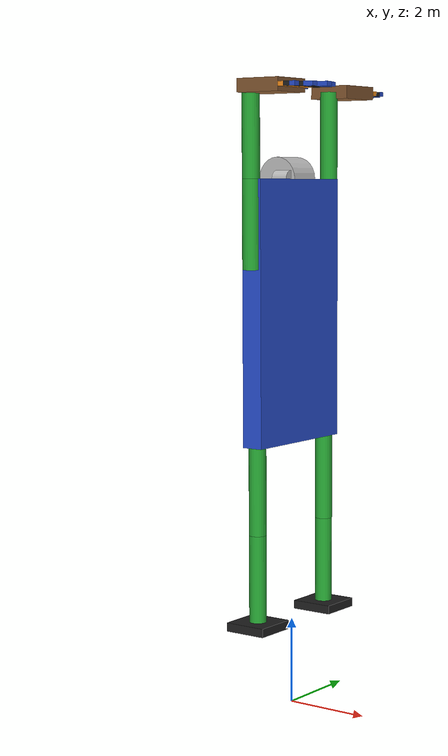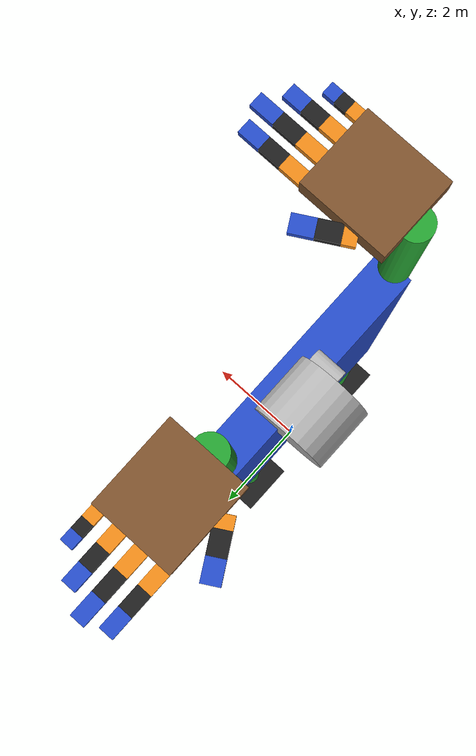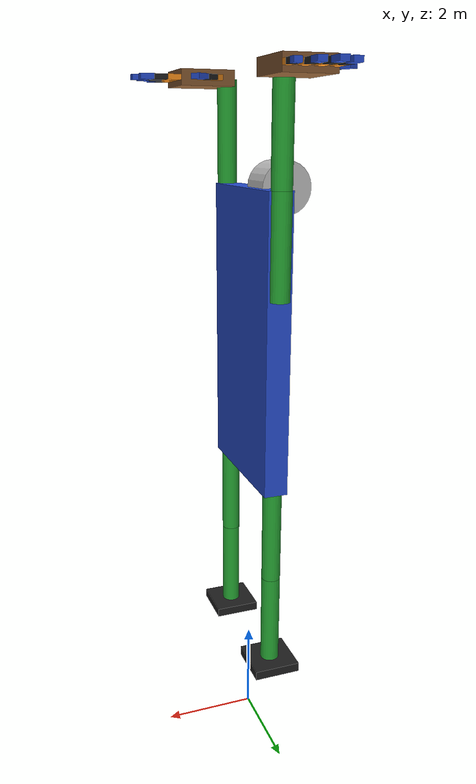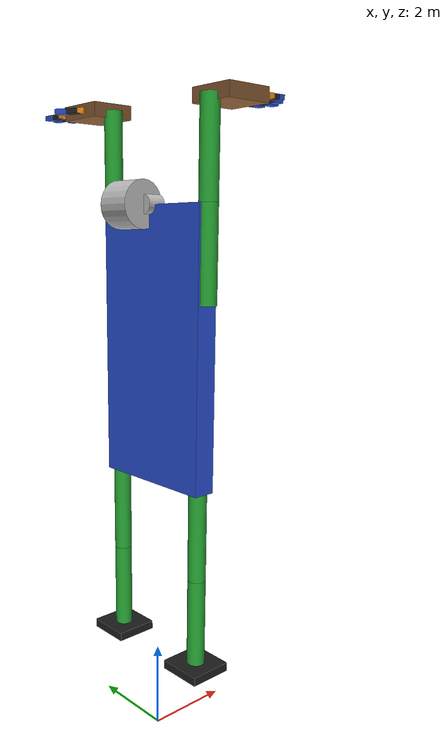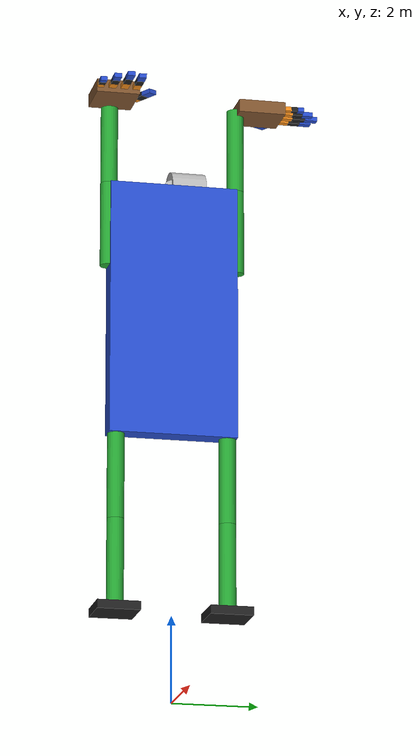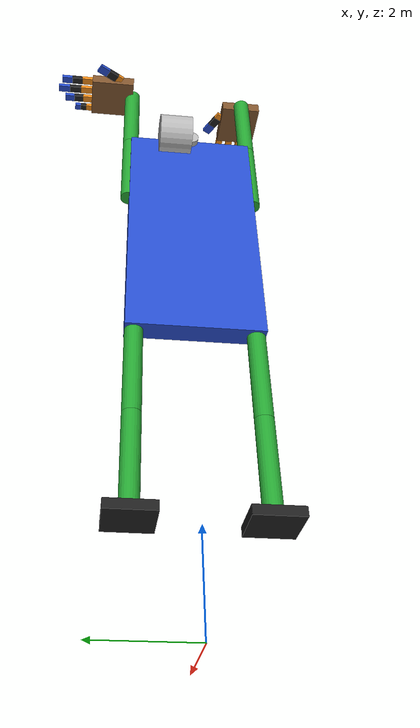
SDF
<?xml version='1.0'?>
<sdf version='1.6'>
  <model name='baby'>
    <link name='root'>
      <pose frame=''>0 0 0 0 -0 0</pose>
      <inertial>
        <pose frame=''>0 0 9.2 0 -0 0</pose>
        <mass>10000</mass>
        <inertia>
          <ixx>37500</ixx>
          <ixy>0</ixy>
          <ixz>0</ixz>
          <iyy>30208.3</iyy>
          <iyz>0</iyz>
          <izz>7708.33</izz>
        </inertia>
      </inertial>
      <gravity>1</gravity>
      <velocity_decay/>
      <self_collide>0</self_collide>
      <enable_wind>0</enable_wind>
      <kinematic>0</kinematic>
      <visual name='root_fixed_joint_lump__Chest_visual'>
        <pose frame=''>0 0 9.2 0 -0 0</pose>
        <geometry>
          <box>
            <size>0.5 3 6</size>
          </box>
        </geometry>
        <material>
          <script>
            <name>Gazebo/Blue</name>
            <uri>file://media/materials/scripts/gazebo.material</uri>
          </script>
          <shader type='pixel'/>
        </material>
        <transparency>0</transparency>
        <cast_shadows>1</cast_shadows>
      </visual>
      <collision name='root_fixed_joint_lump__Chest_collision'>
        <laser_retro>0</laser_retro>
        <max_contacts>10</max_contacts>
        <pose frame=''>0 0 9.2 0 -0 0</pose>
        <geometry>
          <box>
            <size>0.5 3 6</size>
          </box>
        </geometry>
        <surface>
          <friction>
            <ode>
              <mu>1</mu>
              <mu2>1</mu2>
              <fdir1>0 0 0</fdir1>
              <slip1>0</slip1>
              <slip2>0</slip2>
            </ode>
            <torsional>
              <coefficient>1</coefficient>
              <patch_radius>0</patch_radius>
              <surface_radius>0</surface_radius>
              <use_patch_radius>1</use_patch_radius>
              <ode>
                <slip>0</slip>
              </ode>
            </torsional>
          </friction>
          <bounce>
            <restitution_coefficient>0</restitution_coefficient>
            <threshold>1e+06</threshold>
          </bounce>
          <contact>
            <collide_without_contact>0</collide_without_contact>
            <collide_without_contact_bitmask>1</collide_without_contact_bitmask>
            <collide_bitmask>1</collide_bitmask>
            <ode>
              <soft_cfm>0</soft_cfm>
              <soft_erp>0.2</soft_erp>
              <kp>1e+13</kp>
              <kd>1</kd>
              <max_vel>0.01</max_vel>
              <min_depth>0</min_depth>
            </ode>
            <bullet>
              <split_impulse>1</split_impulse>
              <split_impulse_penetration_threshold>-0.01</split_impulse_penetration_threshold>
              <soft_cfm>0</soft_cfm>
              <soft_erp>0.2</soft_erp>
              <kp>1e+13</kp>
              <kd>1</kd>
            </bullet>
          </contact>
        </surface>
      </collision>
    </link>
    <link name='Head'>
      <pose frame=''>-0.4 0 12.2003 -1.57002 -1.57 2.4e-05</pose>
      <inertial>
        <pose frame=''>0 0 0.4 0 -0 0</pose>
        <mass>6</mass>
        <inertia>
          <ixx>0.32</ixx>
          <ixy>0</ixy>
          <ixz>0</ixz>
          <iyy>0.32</iyy>
          <iyz>0</iyz>
          <izz>1.5</izz>
        </inertia>
      </inertial>
      <self_collide>0</self_collide>
      <enable_wind>0</enable_wind>
      <kinematic>0</kinematic>
      <visual name='Head_visual'>
        <pose frame=''>0 0 0.4 0 -0 0</pose>
        <geometry>
          <cylinder>
            <length>0.8</length>
            <radius>0.5</radius>
          </cylinder>
        </geometry>
        <material>
          <shader type='pixel'/>
        </material>
        <transparency>0</transparency>
        <cast_shadows>1</cast_shadows>
      </visual>
      <collision name='Head_collision'>
        <laser_retro>0</laser_retro>
        <max_contacts>10</max_contacts>
        <pose frame=''>0 0 0.4 0 -0 0</pose>
        <geometry>
          <cylinder>
            <radius>0.5</radius>
            <length>0.8</length>
          </cylinder>
        </geometry>
        <surface>
          <friction>
            <ode>
              <mu>1</mu>
              <mu2>1</mu2>
              <fdir1>0 0 0</fdir1>
              <slip1>0</slip1>
              <slip2>0</slip2>
            </ode>
            <torsional>
              <coefficient>1</coefficient>
              <patch_radius>0</patch_radius>
              <surface_radius>0</surface_radius>
              <use_patch_radius>1</use_patch_radius>
              <ode>
                <slip>0</slip>
              </ode>
            </torsional>
          </friction>
          <bounce>
            <restitution_coefficient>0</restitution_coefficient>
            <threshold>1e+06</threshold>
          </bounce>
          <contact>
            <collide_without_contact>0</collide_without_contact>
            <collide_without_contact_bitmask>1</collide_without_contact_bitmask>
            <collide_bitmask>1</collide_bitmask>
            <ode>
              <soft_cfm>0</soft_cfm>
              <soft_erp>0.2</soft_erp>
              <kp>1e+13</kp>
              <kd>1</kd>
              <max_vel>0.01</max_vel>
              <min_depth>0</min_depth>
            </ode>
            <bullet>
              <split_impulse>1</split_impulse>
              <split_impulse_penetration_threshold>-0.01</split_impulse_penetration_threshold>
              <soft_cfm>0</soft_cfm>
              <soft_erp>0.2</soft_erp>
              <kp>1e+13</kp>
              <kd>1</kd>
            </bullet>
          </contact>
        </surface>
      </collision>
    </link>
    <link name='Head_z'>
      <pose frame=''>-0.4 0 12.2003 0 -1.57 0</pose>
      <inertial>
        <pose frame=''>0 0 4e-05 0 -0 0</pose>
        <mass>0.0002</mass>
        <inertia>
          <ixx>1.06667e-13</ixx>
          <ixy>0</ixy>
          <ixz>0</ixz>
          <iyy>1.06667e-13</iyy>
          <iyz>0</iyz>
          <izz>5e-13</izz>
        </inertia>
      </inertial>
      <self_collide>0</self_collide>
      <enable_wind>0</enable_wind>
      <kinematic>0</kinematic>
      <visual name='Head_z_visual'>
        <pose frame=''>0 0 4e-05 0 -0 0</pose>
        <geometry>
          <cylinder>
            <length>8e-05</length>
            <radius>5e-05</radius>
          </cylinder>
        </geometry>
        <material>
          <shader type='pixel'/>
        </material>
        <transparency>0</transparency>
        <cast_shadows>1</cast_shadows>
      </visual>
      <collision name='Head_z_collision'>
        <laser_retro>0</laser_retro>
        <max_contacts>10</max_contacts>
        <pose frame=''>0 0 4e-05 0 -0 0</pose>
        <geometry>
          <cylinder>
            <radius>5e-05</radius>
            <length>8e-05</length>
          </cylinder>
        </geometry>
        <surface>
          <friction>
            <ode>
              <mu>1</mu>
              <mu2>1</mu2>
              <fdir1>0 0 0</fdir1>
              <slip1>0</slip1>
              <slip2>0</slip2>
            </ode>
            <torsional>
              <coefficient>1</coefficient>
              <patch_radius>0</patch_radius>
              <surface_radius>0</surface_radius>
              <use_patch_radius>1</use_patch_radius>
              <ode>
                <slip>0</slip>
              </ode>
            </torsional>
          </friction>
          <bounce>
            <restitution_coefficient>0</restitution_coefficient>
            <threshold>1e+06</threshold>
          </bounce>
          <contact>
            <collide_without_contact>0</collide_without_contact>
            <collide_without_contact_bitmask>1</collide_without_contact_bitmask>
            <collide_bitmask>1</collide_bitmask>
            <ode>
              <soft_cfm>0</soft_cfm>
              <soft_erp>0.2</soft_erp>
              <kp>1e+13</kp>
              <kd>1</kd>
              <max_vel>0.01</max_vel>
              <min_depth>0</min_depth>
            </ode>
            <bullet>
              <split_impulse>1</split_impulse>
              <split_impulse_penetration_threshold>-0.01</split_impulse_penetration_threshold>
              <soft_cfm>0</soft_cfm>
              <soft_erp>0.2</soft_erp>
              <kp>1e+13</kp>
              <kd>1</kd>
            </bullet>
          </contact>
        </surface>
      </collision>
    </link>
    <link name='Left_foot'>
      <pose frame=''>0 -1.3 2.2 0 -0 0</pose>
      <inertial>
        <pose frame=''>0 0 -0.1 0 -0 0</pose>
        <mass>10</mass>
        <inertia>
          <ixx>0.866667</ixx>
          <ixy>0</ixy>
          <ixz>0</ixz>
          <iyy>0.866667</iyy>
          <iyz>0</iyz>
          <izz>1.66667</izz>
        </inertia>
      </inertial>
      <gravity>1</gravity>
      <velocity_decay/>
      <self_collide>0</self_collide>
      <enable_wind>0</enable_wind>
      <kinematic>0</kinematic>
      <visual name='Left_foot_visual'>
        <pose frame=''>0 0 -0.1 0 -0 0</pose>
        <geometry>
          <box>
            <size>1 1 0.2</size>
          </box>
        </geometry>
        <material>
          <script>
            <name>Gazebo/Black</name>
            <uri>file://media/materials/scripts/gazebo.material</uri>
          </script>
          <shader type='pixel'/>
        </material>
        <transparency>0</transparency>
        <cast_shadows>1</cast_shadows>
      </visual>
      <collision name='Left_foot_collision'>
        <laser_retro>0</laser_retro>
        <max_contacts>10</max_contacts>
        <pose frame=''>0 0 -0.1 0 -0 0</pose>
        <geometry>
          <box>
            <size>1 1 0.2</size>
          </box>
        </geometry>
        <surface>
          <friction>
            <ode>
              <mu>1</mu>
              <mu2>1</mu2>
              <fdir1>0 0 0</fdir1>
              <slip1>0</slip1>
              <slip2>0</slip2>
            </ode>
            <torsional>
              <coefficient>1</coefficient>
              <patch_radius>0</patch_radius>
              <surface_radius>0</surface_radius>
              <use_patch_radius>1</use_patch_radius>
              <ode>
                <slip>0</slip>
              </ode>
            </torsional>
          </friction>
          <bounce>
            <restitution_coefficient>0</restitution_coefficient>
            <threshold>1e+06</threshold>
          </bounce>
          <contact>
            <collide_without_contact>0</collide_without_contact>
            <collide_without_contact_bitmask>1</collide_without_contact_bitmask>
            <collide_bitmask>1</collide_bitmask>
            <ode>
              <soft_cfm>0</soft_cfm>
              <soft_erp>0.2</soft_erp>
              <kp>1e+13</kp>
              <kd>1</kd>
              <max_vel>0.01</max_vel>
              <min_depth>0</min_depth>
            </ode>
            <bullet>
              <split_impulse>1</split_impulse>
              <split_impulse_penetration_threshold>-0.01</split_impulse_penetration_threshold>
              <soft_cfm>0</soft_cfm>
              <soft_erp>0.2</soft_erp>
              <kp>1e+13</kp>
              <kd>1</kd>
            </bullet>
          </contact>
        </surface>
      </collision>
    </link>
    <link name='Left_leg_lower'>
      <pose frame=''>0 -1.3 4.2 0 -0 0</pose>
      <inertial>
        <pose frame=''>0 0 -1 0 -0 0</pose>
        <mass>25</mass>
        <inertia>
          <ixx>8.33333</ixx>
          <ixy>0</ixy>
          <ixz>0</ixz>
          <iyy>8.33333</iyy>
          <iyz>0</iyz>
          <izz>1</izz>
        </inertia>
      </inertial>
      <gravity>1</gravity>
      <velocity_decay/>
      <self_collide>0</self_collide>
      <enable_wind>0</enable_wind>
      <kinematic>0</kinematic>
      <visual name='Left_leg_lower_visual'>
        <pose frame=''>0 0 -1 0 -0 0</pose>
        <geometry>
          <cylinder>
            <length>2</length>
            <radius>0.2</radius>
          </cylinder>
        </geometry>
        <material>
          <script>
            <name>Gazebo/Green</name>
            <uri>file://media/materials/scripts/gazebo.material</uri>
          </script>
          <shader type='pixel'/>
        </material>
        <transparency>0</transparency>
        <cast_shadows>1</cast_shadows>
      </visual>
      <collision name='Left_leg_lower_collision'>
        <laser_retro>0</laser_retro>
        <max_contacts>10</max_contacts>
        <pose frame=''>0 0 -1 0 -0 0</pose>
        <geometry>
          <cylinder>
            <radius>0.2</radius>
            <length>2</length>
          </cylinder>
        </geometry>
        <surface>
          <friction>
            <ode>
              <mu>0.2</mu>
              <mu2>0.2</mu2>
              <fdir1>0 0 0</fdir1>
              <slip1>0</slip1>
              <slip2>0</slip2>
            </ode>
            <torsional>
              <coefficient>1</coefficient>
              <patch_radius>0</patch_radius>
              <surface_radius>0</surface_radius>
              <use_patch_radius>1</use_patch_radius>
              <ode>
                <slip>0</slip>
              </ode>
            </torsional>
          </friction>
          <bounce>
            <restitution_coefficient>0</restitution_coefficient>
            <threshold>1e+06</threshold>
          </bounce>
          <contact>
            <collide_without_contact>0</collide_without_contact>
            <collide_without_contact_bitmask>1</collide_without_contact_bitmask>
            <collide_bitmask>1</collide_bitmask>
            <ode>
              <soft_cfm>0</soft_cfm>
              <soft_erp>0.2</soft_erp>
              <kp>1e+13</kp>
              <kd>1</kd>
              <max_vel>0.01</max_vel>
              <min_depth>0</min_depth>
            </ode>
            <bullet>
              <split_impulse>1</split_impulse>
              <split_impulse_penetration_threshold>-0.01</split_impulse_penetration_threshold>
              <soft_cfm>0</soft_cfm>
              <soft_erp>0.2</soft_erp>
              <kp>1e+13</kp>
              <kd>1</kd>
            </bullet>
          </contact>
        </surface>
      </collision>
    </link>
    <link name='Left_leg_upper'>
      <pose frame=''>0 -1.3 6.2 0 -0 0</pose>
      <inertial>
        <pose frame=''>0 0 -1 0 -0 0</pose>
        <mass>25</mass>
        <inertia>
          <ixx>8.33333</ixx>
          <ixy>0</ixy>
          <ixz>0</ixz>
          <iyy>8.33333</iyy>
          <iyz>0</iyz>
          <izz>1</izz>
        </inertia>
      </inertial>
      <gravity>1</gravity>
      <velocity_decay/>
      <self_collide>0</self_collide>
      <enable_wind>0</enable_wind>
      <kinematic>0</kinematic>
      <visual name='Left_leg_upper_visual'>
        <pose frame=''>0 0 -1 0 -0 0</pose>
        <geometry>
          <cylinder>
            <length>2</length>
            <radius>0.2</radius>
          </cylinder>
        </geometry>
        <material>
          <script>
            <name>Gazebo/Green</name>
            <uri>file://media/materials/scripts/gazebo.material</uri>
          </script>
          <shader type='pixel'/>
        </material>
        <transparency>0</transparency>
        <cast_shadows>1</cast_shadows>
      </visual>
      <collision name='Left_leg_upper_collision'>
        <laser_retro>0</laser_retro>
        <max_contacts>10</max_contacts>
        <pose frame=''>0 0 -1 0 -0 0</pose>
        <geometry>
          <cylinder>
            <radius>0.2</radius>
            <length>2</length>
          </cylinder>
        </geometry>
        <surface>
          <friction>
            <ode>
              <mu>1</mu>
              <mu2>1</mu2>
              <fdir1>0 0 0</fdir1>
              <slip1>0</slip1>
              <slip2>0</slip2>
            </ode>
            <torsional>
              <coefficient>1</coefficient>
              <patch_radius>0</patch_radius>
              <surface_radius>0</surface_radius>
              <use_patch_radius>1</use_patch_radius>
              <ode>
                <slip>0</slip>
              </ode>
            </torsional>
          </friction>
          <bounce>
            <restitution_coefficient>0</restitution_coefficient>
            <threshold>1e+06</threshold>
          </bounce>
          <contact>
            <collide_without_contact>0</collide_without_contact>
            <collide_without_contact_bitmask>1</collide_without_contact_bitmask>
            <collide_bitmask>1</collide_bitmask>
            <ode>
              <soft_cfm>0</soft_cfm>
              <soft_erp>0.2</soft_erp>
              <kp>1e+13</kp>
              <kd>1</kd>
              <max_vel>0.01</max_vel>
              <min_depth>0</min_depth>
            </ode>
            <bullet>
              <split_impulse>1</split_impulse>
              <split_impulse_penetration_threshold>-0.01</split_impulse_penetration_threshold>
              <soft_cfm>0</soft_cfm>
              <soft_erp>0.2</soft_erp>
              <kp>1e+13</kp>
              <kd>1</kd>
            </bullet>
          </contact>
        </surface>
      </collision>
    </link>
    <link name='Left_lower'>
      <pose frame=''>0.1 -1.5 12.2 0 -0 0</pose>
      <inertial>
        <pose frame=''>-0.1 0 1 0 -0 0</pose>
        <mass>20</mass>
        <inertia>
          <ixx>6.66667</ixx>
          <ixy>0</ixy>
          <ixz>0</ixz>
          <iyy>6.66667</iyy>
          <iyz>0</iyz>
          <izz>0.8</izz>
        </inertia>
      </inertial>
      <gravity>1</gravity>
      <velocity_decay/>
      <self_collide>0</self_collide>
      <enable_wind>0</enable_wind>
      <kinematic>0</kinematic>
      <visual name='Left_lower_visual'>
        <pose frame=''>-0.1 0 1 0 -0 0</pose>
        <geometry>
          <cylinder>
            <length>2</length>
            <radius>0.2</radius>
          </cylinder>
        </geometry>
        <material>
          <script>
            <name>Gazebo/Green</name>
            <uri>file://media/materials/scripts/gazebo.material</uri>
          </script>
          <shader type='pixel'/>
        </material>
        <transparency>0</transparency>
        <cast_shadows>1</cast_shadows>
      </visual>
      <collision name='Left_lower_collision'>
        <laser_retro>0</laser_retro>
        <max_contacts>10</max_contacts>
        <pose frame=''>-0.1 0 1 0 -0 0</pose>
        <geometry>
          <cylinder>
            <radius>0.2</radius>
            <length>2</length>
          </cylinder>
        </geometry>
        <surface>
          <friction>
            <ode>
              <mu>0.2</mu>
              <mu2>0.2</mu2>
              <fdir1>0 0 0</fdir1>
              <slip1>0</slip1>
              <slip2>0</slip2>
            </ode>
            <torsional>
              <coefficient>1</coefficient>
              <patch_radius>0</patch_radius>
              <surface_radius>0</surface_radius>
              <use_patch_radius>1</use_patch_radius>
              <ode>
                <slip>0</slip>
              </ode>
            </torsional>
          </friction>
          <bounce>
            <restitution_coefficient>0</restitution_coefficient>
            <threshold>1e+06</threshold>
          </bounce>
          <contact>
            <collide_without_contact>0</collide_without_contact>
            <collide_without_contact_bitmask>1</collide_without_contact_bitmask>
            <collide_bitmask>1</collide_bitmask>
            <ode>
              <soft_cfm>0</soft_cfm>
              <soft_erp>0.2</soft_erp>
              <kp>1e+13</kp>
              <kd>1</kd>
              <max_vel>0.01</max_vel>
              <min_depth>0</min_depth>
            </ode>
            <bullet>
              <split_impulse>1</split_impulse>
              <split_impulse_penetration_threshold>-0.01</split_impulse_penetration_threshold>
              <soft_cfm>0</soft_cfm>
              <soft_erp>0.2</soft_erp>
              <kp>1e+13</kp>
              <kd>1</kd>
            </bullet>
          </contact>
        </surface>
      </collision>
    </link>
    <link name='Left_palm'>
      <pose frame=''>0 -1.5 14.2 0 -1.57 3.14</pose>
      <inertial>
        <pose frame=''>0 -0.085711 0.970681 0 -0 0</pose>
        <mass>1.2</mass>
        <inertia>
          <ixx>0.317471</ixx>
          <ixy>0</ixy>
          <ixz>0</ixz>
          <iyy>0.175242</iyy>
          <iyz>-0.0572096</iyz>
          <izz>0.146895</izz>
        </inertia>
      </inertial>
      <velocity_decay/>
      <velocity_decay/>
      <velocity_decay/>
      <velocity_decay/>
      <velocity_decay/>
      <gravity>1</gravity>
      <velocity_decay/>
      <self_collide>0</self_collide>
      <enable_wind>0</enable_wind>
      <kinematic>0</kinematic>
      <visual name='Left_palm_visual'>
        <pose frame=''>0 0 0.55 0 -0 0</pose>
        <geometry>
          <box>
            <size>0.3 1 1.1</size>
          </box>
        </geometry>
        <material>
          <script>
            <name>Gazebo/Brown</name>
            <uri>file://media/materials/scripts/gazebo.material</uri>
          </script>
          <shader type='pixel'/>
        </material>
        <transparency>0</transparency>
        <cast_shadows>1</cast_shadows>
      </visual>
      <visual name='Left_palm_fixed_joint_lump__Left_seg11_visual_1'>
        <pose frame=''>0 -0.4135 1.234 0 -0 0</pose>
        <geometry>
          <box>
            <size>0.1 0.173 0.268</size>
          </box>
        </geometry>
        <material>
          <script>
            <name>Gazebo/Orange</name>
            <uri>file://media/materials/scripts/gazebo.material</uri>
          </script>
          <shader type='pixel'/>
        </material>
        <transparency>0</transparency>
        <cast_shadows>1</cast_shadows>
      </visual>
      <visual name='Left_palm_fixed_joint_lump__Left_seg21_visual_2'>
        <pose frame=''>0 -0.134 1.25 0 -0 0</pose>
        <geometry>
          <box>
            <size>0.1 0.173 0.3</size>
          </box>
        </geometry>
        <material>
          <script>
            <name>Gazebo/Orange</name>
            <uri>file://media/materials/scripts/gazebo.material</uri>
          </script>
          <shader type='pixel'/>
        </material>
        <transparency>0</transparency>
        <cast_shadows>1</cast_shadows>
      </visual>
      <visual name='Left_palm_fixed_joint_lump__Left_seg41_visual_4'>
        <pose frame=''>0 0.425 1.175 0 -0 0</pose>
        <geometry>
          <box>
            <size>0.1 0.15 0.15</size>
          </box>
        </geometry>
        <material>
          <script>
            <name>Gazebo/Orange</name>
            <uri>file://media/materials/scripts/gazebo.material</uri>
          </script>
          <shader type='pixel'/>
        </material>
        <transparency>0</transparency>
        <cast_shadows>1</cast_shadows>
      </visual>
      <visual name='Left_palm_fixed_joint_lump__Left_seg31_visual_3'>
        <pose frame=''>0 0.1455 1.22 0 -0 0</pose>
        <geometry>
          <box>
            <size>0.1 0.173 0.24</size>
          </box>
        </geometry>
        <material>
          <script>
            <name>Gazebo/Orange</name>
            <uri>file://media/materials/scripts/gazebo.material</uri>
          </script>
          <shader type='pixel'/>
        </material>
        <transparency>0</transparency>
        <cast_shadows>1</cast_shadows>
      </visual>
      <visual name='Left_palm_fixed_joint_lump__Left_segt1_visual_5'>
        <pose frame=''>0 -0.537266 0.395086 0.52 -0 0</pose>
        <geometry>
          <box>
            <size>0.1 0.21 0.15</size>
          </box>
        </geometry>
        <material>
          <script>
            <name>Gazebo/Orange</name>
            <uri>file://media/materials/scripts/gazebo.material</uri>
          </script>
          <shader type='pixel'/>
        </material>
        <transparency>0</transparency>
        <cast_shadows>1</cast_shadows>
      </visual>
      <collision name='Left_palm_collision'>
        <laser_retro>0</laser_retro>
        <max_contacts>10</max_contacts>
        <pose frame=''>0 0 0.55 0 -0 0</pose>
        <geometry>
          <box>
            <size>0.3 1 1.1</size>
          </box>
        </geometry>
        <surface>
          <friction>
            <ode>
              <mu>1</mu>
              <mu2>1</mu2>
              <fdir1>0 0 0</fdir1>
              <slip1>0</slip1>
              <slip2>0</slip2>
            </ode>
            <torsional>
              <coefficient>1</coefficient>
              <patch_radius>0</patch_radius>
              <surface_radius>0</surface_radius>
              <use_patch_radius>1</use_patch_radius>
              <ode>
                <slip>0</slip>
              </ode>
            </torsional>
          </friction>
          <bounce>
            <restitution_coefficient>0</restitution_coefficient>
            <threshold>1e+06</threshold>
          </bounce>
          <contact>
            <collide_without_contact>0</collide_without_contact>
            <collide_without_contact_bitmask>1</collide_without_contact_bitmask>
            <collide_bitmask>1</collide_bitmask>
            <ode>
              <soft_cfm>0</soft_cfm>
              <soft_erp>0.2</soft_erp>
              <kp>1e+13</kp>
              <kd>1</kd>
              <max_vel>0.01</max_vel>
              <min_depth>0</min_depth>
            </ode>
            <bullet>
              <split_impulse>1</split_impulse>
              <split_impulse_penetration_threshold>-0.01</split_impulse_penetration_threshold>
              <soft_cfm>0</soft_cfm>
              <soft_erp>0.2</soft_erp>
              <kp>1e+13</kp>
              <kd>1</kd>
            </bullet>
          </contact>
        </surface>
      </collision>
      <collision name='Left_palm_fixed_joint_lump__Left_seg11_collision_1'>
        <laser_retro>0</laser_retro>
        <max_contacts>10</max_contacts>
        <pose frame=''>0 -0.4135 1.234 0 -0 0</pose>
        <geometry>
          <box>
            <size>0.1 0.173 0.268</size>
          </box>
        </geometry>
        <surface>
          <friction>
            <ode>
              <mu>1</mu>
              <mu2>1</mu2>
              <fdir1>0 0 0</fdir1>
              <slip1>0</slip1>
              <slip2>0</slip2>
            </ode>
            <torsional>
              <coefficient>1</coefficient>
              <patch_radius>0</patch_radius>
              <surface_radius>0</surface_radius>
              <use_patch_radius>1</use_patch_radius>
              <ode>
                <slip>0</slip>
              </ode>
            </torsional>
          </friction>
          <bounce>
            <restitution_coefficient>0</restitution_coefficient>
            <threshold>1e+06</threshold>
          </bounce>
          <contact>
            <collide_without_contact>0</collide_without_contact>
            <collide_without_contact_bitmask>1</collide_without_contact_bitmask>
            <collide_bitmask>1</collide_bitmask>
            <ode>
              <soft_cfm>0</soft_cfm>
              <soft_erp>0.2</soft_erp>
              <kp>1e+13</kp>
              <kd>1</kd>
              <max_vel>0.01</max_vel>
              <min_depth>0</min_depth>
            </ode>
            <bullet>
              <split_impulse>1</split_impulse>
              <split_impulse_penetration_threshold>-0.01</split_impulse_penetration_threshold>
              <soft_cfm>0</soft_cfm>
              <soft_erp>0.2</soft_erp>
              <kp>1e+13</kp>
              <kd>1</kd>
            </bullet>
          </contact>
        </surface>
      </collision>
      <collision name='Left_palm_fixed_joint_lump__Left_seg21_collision_2'>
        <laser_retro>0</laser_retro>
        <max_contacts>10</max_contacts>
        <pose frame=''>0 -0.134 1.25 0 -0 0</pose>
        <geometry>
          <box>
            <size>0.1 0.173 0.2</size>
          </box>
        </geometry>
        <surface>
          <friction>
            <ode>
              <mu>1</mu>
              <mu2>1</mu2>
              <fdir1>0 0 0</fdir1>
              <slip1>0</slip1>
              <slip2>0</slip2>
            </ode>
            <torsional>
              <coefficient>1</coefficient>
              <patch_radius>0</patch_radius>
              <surface_radius>0</surface_radius>
              <use_patch_radius>1</use_patch_radius>
              <ode>
                <slip>0</slip>
              </ode>
            </torsional>
          </friction>
          <bounce>
            <restitution_coefficient>0</restitution_coefficient>
            <threshold>1e+06</threshold>
          </bounce>
          <contact>
            <collide_without_contact>0</collide_without_contact>
            <collide_without_contact_bitmask>1</collide_without_contact_bitmask>
            <collide_bitmask>1</collide_bitmask>
            <ode>
              <soft_cfm>0</soft_cfm>
              <soft_erp>0.2</soft_erp>
              <kp>1e+13</kp>
              <kd>1</kd>
              <max_vel>0.01</max_vel>
              <min_depth>0</min_depth>
            </ode>
            <bullet>
              <split_impulse>1</split_impulse>
              <split_impulse_penetration_threshold>-0.01</split_impulse_penetration_threshold>
              <soft_cfm>0</soft_cfm>
              <soft_erp>0.2</soft_erp>
              <kp>1e+13</kp>
              <kd>1</kd>
            </bullet>
          </contact>
        </surface>
      </collision>
      <collision name='Left_palm_fixed_joint_lump__Left_seg31_collision_3'>
        <laser_retro>0</laser_retro>
        <max_contacts>10</max_contacts>
        <pose frame=''>0 0.1455 1.22 0 -0 0</pose>
        <geometry>
          <box>
            <size>0.1 0.173 0.24</size>
          </box>
        </geometry>
        <surface>
          <friction>
            <ode>
              <mu>1</mu>
              <mu2>1</mu2>
              <fdir1>0 0 0</fdir1>
              <slip1>0</slip1>
              <slip2>0</slip2>
            </ode>
            <torsional>
              <coefficient>1</coefficient>
              <patch_radius>0</patch_radius>
              <surface_radius>0</surface_radius>
              <use_patch_radius>1</use_patch_radius>
              <ode>
                <slip>0</slip>
              </ode>
            </torsional>
          </friction>
          <bounce>
            <restitution_coefficient>0</restitution_coefficient>
            <threshold>1e+06</threshold>
          </bounce>
          <contact>
            <collide_without_contact>0</collide_without_contact>
            <collide_without_contact_bitmask>1</collide_without_contact_bitmask>
            <collide_bitmask>1</collide_bitmask>
            <ode>
              <soft_cfm>0</soft_cfm>
              <soft_erp>0.2</soft_erp>
              <kp>1e+13</kp>
              <kd>1</kd>
              <max_vel>0.01</max_vel>
              <min_depth>0</min_depth>
            </ode>
            <bullet>
              <split_impulse>1</split_impulse>
              <split_impulse_penetration_threshold>-0.01</split_impulse_penetration_threshold>
              <soft_cfm>0</soft_cfm>
              <soft_erp>0.2</soft_erp>
              <kp>1e+13</kp>
              <kd>1</kd>
            </bullet>
          </contact>
        </surface>
      </collision>
      <collision name='Left_palm_fixed_joint_lump__Left_seg41_collision_4'>
        <laser_retro>0</laser_retro>
        <max_contacts>10</max_contacts>
        <pose frame=''>0 0.425 1.175 0 -0 0</pose>
        <geometry>
          <box>
            <size>0.1 0.15 0.15</size>
          </box>
        </geometry>
        <surface>
          <friction>
            <ode>
              <mu>1</mu>
              <mu2>1</mu2>
              <fdir1>0 0 0</fdir1>
              <slip1>0</slip1>
              <slip2>0</slip2>
            </ode>
            <torsional>
              <coefficient>1</coefficient>
              <patch_radius>0</patch_radius>
              <surface_radius>0</surface_radius>
              <use_patch_radius>1</use_patch_radius>
              <ode>
                <slip>0</slip>
              </ode>
            </torsional>
          </friction>
          <bounce>
            <restitution_coefficient>0</restitution_coefficient>
            <threshold>1e+06</threshold>
          </bounce>
          <contact>
            <collide_without_contact>0</collide_without_contact>
            <collide_without_contact_bitmask>1</collide_without_contact_bitmask>
            <collide_bitmask>1</collide_bitmask>
            <ode>
              <soft_cfm>0</soft_cfm>
              <soft_erp>0.2</soft_erp>
              <kp>1e+13</kp>
              <kd>1</kd>
              <max_vel>0.01</max_vel>
              <min_depth>0</min_depth>
            </ode>
            <bullet>
              <split_impulse>1</split_impulse>
              <split_impulse_penetration_threshold>-0.01</split_impulse_penetration_threshold>
              <soft_cfm>0</soft_cfm>
              <soft_erp>0.2</soft_erp>
              <kp>1e+13</kp>
              <kd>1</kd>
            </bullet>
          </contact>
        </surface>
      </collision>
      <collision name='Left_palm_fixed_joint_lump__Left_segt1_collision_5'>
        <laser_retro>0</laser_retro>
        <max_contacts>10</max_contacts>
        <pose frame=''>0 -0.537266 0.395086 0.52 -0 0</pose>
        <geometry>
          <box>
            <size>0.1 0.21 0.15</size>
          </box>
        </geometry>
        <surface>
          <friction>
            <ode>
              <mu>1</mu>
              <mu2>1</mu2>
              <fdir1>0 0 0</fdir1>
              <slip1>0</slip1>
              <slip2>0</slip2>
            </ode>
            <torsional>
              <coefficient>1</coefficient>
              <patch_radius>0</patch_radius>
              <surface_radius>0</surface_radius>
              <use_patch_radius>1</use_patch_radius>
              <ode>
                <slip>0</slip>
              </ode>
            </torsional>
          </friction>
          <bounce>
            <restitution_coefficient>0</restitution_coefficient>
            <threshold>1e+06</threshold>
          </bounce>
          <contact>
            <collide_without_contact>0</collide_without_contact>
            <collide_without_contact_bitmask>1</collide_without_contact_bitmask>
            <collide_bitmask>1</collide_bitmask>
            <ode>
              <soft_cfm>0</soft_cfm>
              <soft_erp>0.2</soft_erp>
              <kp>1e+13</kp>
              <kd>1</kd>
              <max_vel>0.01</max_vel>
              <min_depth>0</min_depth>
            </ode>
            <bullet>
              <split_impulse>1</split_impulse>
              <split_impulse_penetration_threshold>-0.01</split_impulse_penetration_threshold>
              <soft_cfm>0</soft_cfm>
              <soft_erp>0.2</soft_erp>
              <kp>1e+13</kp>
              <kd>1</kd>
            </bullet>
          </contact>
        </surface>
      </collision>
    </link>
    <link name='Left_seg12'>
      <pose frame=''>1.36862 -1.08868 14.2511 0 -1.57 3.14</pose>
      <inertial>
        <pose frame=''>-0.05 0 0.134 0 -0 0</pose>
        <mass>0.2</mass>
        <inertia>
          <ixx>0.000333333</ixx>
          <ixy>0</ixy>
          <ixz>0</ixz>
          <iyy>0.000833333</iyy>
          <iyz>0</iyz>
          <izz>0.000833333</izz>
        </inertia>
      </inertial>
      <gravity>1</gravity>
      <velocity_decay/>
      <self_collide>0</self_collide>
      <enable_wind>0</enable_wind>
      <kinematic>0</kinematic>
      <visual name='Left_seg12_visual'>
        <pose frame=''>-0.05 0 0.134 0 -0 0</pose>
        <geometry>
          <box>
            <size>0.1 0.173 0.268</size>
          </box>
        </geometry>
        <material>
          <script>
            <name>Gazebo/Black</name>
            <uri>file://media/materials/scripts/gazebo.material</uri>
          </script>
          <shader type='pixel'/>
        </material>
        <transparency>0</transparency>
        <cast_shadows>1</cast_shadows>
      </visual>
      <collision name='Left_seg12_collision'>
        <laser_retro>0</laser_retro>
        <max_contacts>10</max_contacts>
        <pose frame=''>-0.05 0 0.134 0 -0 0</pose>
        <geometry>
          <box>
            <size>0.1 0.173 0.268</size>
          </box>
        </geometry>
        <surface>
          <friction>
            <ode>
              <mu>0.2</mu>
              <mu2>0.2</mu2>
              <fdir1>0 0 0</fdir1>
              <slip1>0</slip1>
              <slip2>0</slip2>
            </ode>
            <torsional>
              <coefficient>1</coefficient>
              <patch_radius>0</patch_radius>
              <surface_radius>0</surface_radius>
              <use_patch_radius>1</use_patch_radius>
              <ode>
                <slip>0</slip>
              </ode>
            </torsional>
          </friction>
          <bounce>
            <restitution_coefficient>0</restitution_coefficient>
            <threshold>1e+06</threshold>
          </bounce>
          <contact>
            <collide_without_contact>0</collide_without_contact>
            <collide_without_contact_bitmask>1</collide_without_contact_bitmask>
            <collide_bitmask>1</collide_bitmask>
            <ode>
              <soft_cfm>0</soft_cfm>
              <soft_erp>0.2</soft_erp>
              <kp>1e+13</kp>
              <kd>1</kd>
              <max_vel>0.01</max_vel>
              <min_depth>0</min_depth>
            </ode>
            <bullet>
              <split_impulse>1</split_impulse>
              <split_impulse_penetration_threshold>-0.01</split_impulse_penetration_threshold>
              <soft_cfm>0</soft_cfm>
              <soft_erp>0.2</soft_erp>
              <kp>1e+13</kp>
              <kd>1</kd>
            </bullet>
          </contact>
        </surface>
      </collision>
    </link>
    <link name='Left_seg13'>
      <pose frame=''>1.63662 -1.08911 14.2513 0 -1.57 3.14</pose>
      <inertial>
        <pose frame=''>-0.05 0 0.134 0 -0 0</pose>
        <mass>0.2</mass>
        <inertia>
          <ixx>0.000333333</ixx>
          <ixy>0</ixy>
          <ixz>0</ixz>
          <iyy>0.000833333</iyy>
          <iyz>0</iyz>
          <izz>0.000833333</izz>
        </inertia>
      </inertial>
      <gravity>1</gravity>
      <velocity_decay/>
      <self_collide>0</self_collide>
      <enable_wind>0</enable_wind>
      <kinematic>0</kinematic>
      <visual name='Left_seg13_visual'>
        <pose frame=''>-0.05 0 0.134 0 -0 0</pose>
        <geometry>
          <box>
            <size>0.1 0.173 0.268</size>
          </box>
        </geometry>
        <material>
          <script>
            <name>Gazebo/Blue</name>
            <uri>file://media/materials/scripts/gazebo.material</uri>
          </script>
          <shader type='pixel'/>
        </material>
        <transparency>0</transparency>
        <cast_shadows>1</cast_shadows>
      </visual>
      <collision name='Left_seg13_collision'>
        <laser_retro>0</laser_retro>
        <max_contacts>10</max_contacts>
        <pose frame=''>-0.05 0 0.134 0 -0 0</pose>
        <geometry>
          <box>
            <size>0.1 0.173 0.268</size>
          </box>
        </geometry>
        <surface>
          <friction>
            <ode>
              <mu>1</mu>
              <mu2>1</mu2>
              <fdir1>0 0 0</fdir1>
              <slip1>0</slip1>
              <slip2>0</slip2>
            </ode>
            <torsional>
              <coefficient>1</coefficient>
              <patch_radius>0</patch_radius>
              <surface_radius>0</surface_radius>
              <use_patch_radius>1</use_patch_radius>
              <ode>
                <slip>0</slip>
              </ode>
            </torsional>
          </friction>
          <bounce>
            <restitution_coefficient>0</restitution_coefficient>
            <threshold>1e+06</threshold>
          </bounce>
          <contact>
            <collide_without_contact>0</collide_without_contact>
            <collide_without_contact_bitmask>1</collide_without_contact_bitmask>
            <collide_bitmask>1</collide_bitmask>
            <ode>
              <soft_cfm>0</soft_cfm>
              <soft_erp>0.2</soft_erp>
              <kp>1e+13</kp>
              <kd>1</kd>
              <max_vel>0.01</max_vel>
              <min_depth>0</min_depth>
            </ode>
            <bullet>
              <split_impulse>1</split_impulse>
              <split_impulse_penetration_threshold>-0.01</split_impulse_penetration_threshold>
              <soft_cfm>0</soft_cfm>
              <soft_erp>0.2</soft_erp>
              <kp>1e+13</kp>
              <kd>1</kd>
            </bullet>
          </contact>
        </surface>
      </collision>
    </link>
    <link name='Left_seg22'>
      <pose frame=''>1.40017 -1.36823 14.2511 0 -1.57 3.14</pose>
      <inertial>
        <pose frame=''>-0.05 0 0.15 0 -0 0</pose>
        <mass>0.2</mass>
        <inertia>
          <ixx>0.000333333</ixx>
          <ixy>0</ixy>
          <ixz>0</ixz>
          <iyy>0.000833333</iyy>
          <iyz>0</iyz>
          <izz>0.000833333</izz>
        </inertia>
      </inertial>
      <gravity>1</gravity>
      <velocity_decay/>
      <self_collide>0</self_collide>
      <enable_wind>0</enable_wind>
      <kinematic>0</kinematic>
      <visual name='Left_seg22_visual'>
        <pose frame=''>-0.05 0 0.15 0 -0 0</pose>
        <geometry>
          <box>
            <size>0.1 0.173 0.3</size>
          </box>
        </geometry>
        <material>
          <script>
            <name>Gazebo/Black</name>
            <uri>file://media/materials/scripts/gazebo.material</uri>
          </script>
          <shader type='pixel'/>
        </material>
        <transparency>0</transparency>
        <cast_shadows>1</cast_shadows>
      </visual>
      <collision name='Left_seg22_collision'>
        <laser_retro>0</laser_retro>
        <max_contacts>10</max_contacts>
        <pose frame=''>-0.05 0 0.15 0 -0 0</pose>
        <geometry>
          <box>
            <size>0.1 0.173 0.3</size>
          </box>
        </geometry>
        <surface>
          <friction>
            <ode>
              <mu>0.2</mu>
              <mu2>0.2</mu2>
              <fdir1>0 0 0</fdir1>
              <slip1>0</slip1>
              <slip2>0</slip2>
            </ode>
            <torsional>
              <coefficient>1</coefficient>
              <patch_radius>0</patch_radius>
              <surface_radius>0</surface_radius>
              <use_patch_radius>1</use_patch_radius>
              <ode>
                <slip>0</slip>
              </ode>
            </torsional>
          </friction>
          <bounce>
            <restitution_coefficient>0</restitution_coefficient>
            <threshold>1e+06</threshold>
          </bounce>
          <contact>
            <collide_without_contact>0</collide_without_contact>
            <collide_without_contact_bitmask>1</collide_without_contact_bitmask>
            <collide_bitmask>1</collide_bitmask>
            <ode>
              <soft_cfm>0</soft_cfm>
              <soft_erp>0.2</soft_erp>
              <kp>1e+13</kp>
              <kd>1</kd>
              <max_vel>0.01</max_vel>
              <min_depth>0</min_depth>
            </ode>
            <bullet>
              <split_impulse>1</split_impulse>
              <split_impulse_penetration_threshold>-0.01</split_impulse_penetration_threshold>
              <soft_cfm>0</soft_cfm>
              <soft_erp>0.2</soft_erp>
              <kp>1e+13</kp>
              <kd>1</kd>
            </bullet>
          </contact>
        </surface>
      </collision>
    </link>
    <link name='Left_seg23'>
      <pose frame=''>1.70017 -1.36871 14.2514 0 -1.57 3.14</pose>
      <inertial>
        <pose frame=''>-0.05 0 0.15 0 -0 0</pose>
        <mass>0.2</mass>
        <inertia>
          <ixx>0.000333333</ixx>
          <ixy>0</ixy>
          <ixz>0</ixz>
          <iyy>0.000833333</iyy>
          <iyz>0</iyz>
          <izz>0.000833333</izz>
        </inertia>
      </inertial>
      <gravity>1</gravity>
      <velocity_decay/>
      <self_collide>0</self_collide>
      <enable_wind>0</enable_wind>
      <kinematic>0</kinematic>
      <visual name='Left_seg23_visual'>
        <pose frame=''>-0.05 0 0.15 0 -0 0</pose>
        <geometry>
          <box>
            <size>0.1 0.173 0.3</size>
          </box>
        </geometry>
        <material>
          <script>
            <name>Gazebo/Blue</name>
            <uri>file://media/materials/scripts/gazebo.material</uri>
          </script>
          <shader type='pixel'/>
        </material>
        <transparency>0</transparency>
        <cast_shadows>1</cast_shadows>
      </visual>
      <collision name='Left_seg23_collision'>
        <laser_retro>0</laser_retro>
        <max_contacts>10</max_contacts>
        <pose frame=''>-0.05 0 0.15 0 -0 0</pose>
        <geometry>
          <box>
            <size>0.1 0.173 0.3</size>
          </box>
        </geometry>
        <surface>
          <friction>
            <ode>
              <mu>1</mu>
              <mu2>1</mu2>
              <fdir1>0 0 0</fdir1>
              <slip1>0</slip1>
              <slip2>0</slip2>
            </ode>
            <torsional>
              <coefficient>1</coefficient>
              <patch_radius>0</patch_radius>
              <surface_radius>0</surface_radius>
              <use_patch_radius>1</use_patch_radius>
              <ode>
                <slip>0</slip>
              </ode>
            </torsional>
          </friction>
          <bounce>
            <restitution_coefficient>0</restitution_coefficient>
            <threshold>1e+06</threshold>
          </bounce>
          <contact>
            <collide_without_contact>0</collide_without_contact>
            <collide_without_contact_bitmask>1</collide_without_contact_bitmask>
            <collide_bitmask>1</collide_bitmask>
            <ode>
              <soft_cfm>0</soft_cfm>
              <soft_erp>0.2</soft_erp>
              <kp>1e+13</kp>
              <kd>1</kd>
              <max_vel>0.01</max_vel>
              <min_depth>0</min_depth>
            </ode>
            <bullet>
              <split_impulse>1</split_impulse>
              <split_impulse_penetration_threshold>-0.01</split_impulse_penetration_threshold>
              <soft_cfm>0</soft_cfm>
              <soft_erp>0.2</soft_erp>
              <kp>1e+13</kp>
              <kd>1</kd>
            </bullet>
          </contact>
        </surface>
      </collision>
    </link>
    <link name='Left_seg32'>
      <pose frame=''>1.33973 -1.64763 14.2511 0 -1.57 3.14</pose>
      <inertial>
        <pose frame=''>-0.05 0 0.12 0 -0 0</pose>
        <mass>0.2</mass>
        <inertia>
          <ixx>0.000333333</ixx>
          <ixy>0</ixy>
          <ixz>0</ixz>
          <iyy>0.000833333</iyy>
          <iyz>0</iyz>
          <izz>0.000833333</izz>
        </inertia>
      </inertial>
      <gravity>1</gravity>
      <velocity_decay/>
      <self_collide>0</self_collide>
      <enable_wind>0</enable_wind>
      <kinematic>0</kinematic>
      <visual name='Left_seg32_visual'>
        <pose frame=''>-0.05 0 0.12 0 -0 0</pose>
        <geometry>
          <box>
            <size>0.1 0.173 0.24</size>
          </box>
        </geometry>
        <material>
          <script>
            <name>Gazebo/Black</name>
            <uri>file://media/materials/scripts/gazebo.material</uri>
          </script>
          <shader type='pixel'/>
        </material>
        <transparency>0</transparency>
        <cast_shadows>1</cast_shadows>
      </visual>
      <collision name='Left_seg32_collision'>
        <laser_retro>0</laser_retro>
        <max_contacts>10</max_contacts>
        <pose frame=''>-0.05 0 0.12 0 -0 0</pose>
        <geometry>
          <box>
            <size>0.1 0.173 0.24</size>
          </box>
        </geometry>
        <surface>
          <friction>
            <ode>
              <mu>0.2</mu>
              <mu2>0.2</mu2>
              <fdir1>0 0 0</fdir1>
              <slip1>0</slip1>
              <slip2>0</slip2>
            </ode>
            <torsional>
              <coefficient>1</coefficient>
              <patch_radius>0</patch_radius>
              <surface_radius>0</surface_radius>
              <use_patch_radius>1</use_patch_radius>
              <ode>
                <slip>0</slip>
              </ode>
            </torsional>
          </friction>
          <bounce>
            <restitution_coefficient>0</restitution_coefficient>
            <threshold>1e+06</threshold>
          </bounce>
          <contact>
            <collide_without_contact>0</collide_without_contact>
            <collide_without_contact_bitmask>1</collide_without_contact_bitmask>
            <collide_bitmask>1</collide_bitmask>
            <ode>
              <soft_cfm>0</soft_cfm>
              <soft_erp>0.2</soft_erp>
              <kp>1e+13</kp>
              <kd>1</kd>
              <max_vel>0.01</max_vel>
              <min_depth>0</min_depth>
            </ode>
            <bullet>
              <split_impulse>1</split_impulse>
              <split_impulse_penetration_threshold>-0.01</split_impulse_penetration_threshold>
              <soft_cfm>0</soft_cfm>
              <soft_erp>0.2</soft_erp>
              <kp>1e+13</kp>
              <kd>1</kd>
            </bullet>
          </contact>
        </surface>
      </collision>
    </link>
    <link name='Left_seg33'>
      <pose frame=''>1.57973 -1.64802 14.2513 0 -1.57 3.14</pose>
      <inertial>
        <pose frame=''>-0.05 0 0.12 0 -0 0</pose>
        <mass>0.2</mass>
        <inertia>
          <ixx>0.000333333</ixx>
          <ixy>0</ixy>
          <ixz>0</ixz>
          <iyy>0.000833333</iyy>
          <iyz>0</iyz>
          <izz>0.000833333</izz>
        </inertia>
      </inertial>
      <gravity>1</gravity>
      <velocity_decay/>
      <self_collide>0</self_collide>
      <enable_wind>0</enable_wind>
      <kinematic>0</kinematic>
      <visual name='Left_seg33_visual'>
        <pose frame=''>-0.05 0 0.12 0 -0 0</pose>
        <geometry>
          <box>
            <size>0.1 0.173 0.24</size>
          </box>
        </geometry>
        <material>
          <script>
            <name>Gazebo/Blue</name>
            <uri>file://media/materials/scripts/gazebo.material</uri>
          </script>
          <shader type='pixel'/>
        </material>
        <transparency>0</transparency>
        <cast_shadows>1</cast_shadows>
      </visual>
      <collision name='Left_seg33_collision'>
        <laser_retro>0</laser_retro>
        <max_contacts>10</max_contacts>
        <pose frame=''>-0.05 0 0.12 0 -0 0</pose>
        <geometry>
          <box>
            <size>0.1 0.173 0.24</size>
          </box>
        </geometry>
        <surface>
          <friction>
            <ode>
              <mu>1</mu>
              <mu2>1</mu2>
              <fdir1>0 0 0</fdir1>
              <slip1>0</slip1>
              <slip2>0</slip2>
            </ode>
            <torsional>
              <coefficient>1</coefficient>
              <patch_radius>0</patch_radius>
              <surface_radius>0</surface_radius>
              <use_patch_radius>1</use_patch_radius>
              <ode>
                <slip>0</slip>
              </ode>
            </torsional>
          </friction>
          <bounce>
            <restitution_coefficient>0</restitution_coefficient>
            <threshold>1e+06</threshold>
          </bounce>
          <contact>
            <collide_without_contact>0</collide_without_contact>
            <collide_without_contact_bitmask>1</collide_without_contact_bitmask>
            <collide_bitmask>1</collide_bitmask>
            <ode>
              <soft_cfm>0</soft_cfm>
              <soft_erp>0.2</soft_erp>
              <kp>1e+13</kp>
              <kd>1</kd>
              <max_vel>0.01</max_vel>
              <min_depth>0</min_depth>
            </ode>
            <bullet>
              <split_impulse>1</split_impulse>
              <split_impulse_penetration_threshold>-0.01</split_impulse_penetration_threshold>
              <soft_cfm>0</soft_cfm>
              <soft_erp>0.2</soft_erp>
              <kp>1e+13</kp>
              <kd>1</kd>
            </bullet>
          </contact>
        </surface>
      </collision>
    </link>
    <link name='Left_seg42'>
      <pose frame=''>1.24928 -1.92699 14.251 0 -1.57 3.14</pose>
      <inertial>
        <pose frame=''>-0.05 0 0.075 0 -0 0</pose>
        <mass>0.2</mass>
        <inertia>
          <ixx>0.000333333</ixx>
          <ixy>0</ixy>
          <ixz>0</ixz>
          <iyy>0.000833333</iyy>
          <iyz>0</iyz>
          <izz>0.000833333</izz>
        </inertia>
      </inertial>
      <gravity>1</gravity>
      <velocity_decay/>
      <self_collide>0</self_collide>
      <enable_wind>0</enable_wind>
      <kinematic>0</kinematic>
      <visual name='Left_seg42_visual'>
        <pose frame=''>-0.05 0 0.075 0 -0 0</pose>
        <geometry>
          <box>
            <size>0.1 0.15 0.15</size>
          </box>
        </geometry>
        <material>
          <script>
            <name>Gazebo/Black</name>
            <uri>file://media/materials/scripts/gazebo.material</uri>
          </script>
          <shader type='pixel'/>
        </material>
        <transparency>0</transparency>
        <cast_shadows>1</cast_shadows>
      </visual>
      <collision name='Left_seg42_collision'>
        <laser_retro>0</laser_retro>
        <max_contacts>10</max_contacts>
        <pose frame=''>-0.05 0 0.075 0 -0 0</pose>
        <geometry>
          <box>
            <size>0.1 0.15 0.15</size>
          </box>
        </geometry>
        <surface>
          <friction>
            <ode>
              <mu>0.2</mu>
              <mu2>0.2</mu2>
              <fdir1>0 0 0</fdir1>
              <slip1>0</slip1>
              <slip2>0</slip2>
            </ode>
            <torsional>
              <coefficient>1</coefficient>
              <patch_radius>0</patch_radius>
              <surface_radius>0</surface_radius>
              <use_patch_radius>1</use_patch_radius>
              <ode>
                <slip>0</slip>
              </ode>
            </torsional>
          </friction>
          <bounce>
            <restitution_coefficient>0</restitution_coefficient>
            <threshold>1e+06</threshold>
          </bounce>
          <contact>
            <collide_without_contact>0</collide_without_contact>
            <collide_without_contact_bitmask>1</collide_without_contact_bitmask>
            <collide_bitmask>1</collide_bitmask>
            <ode>
              <soft_cfm>0</soft_cfm>
              <soft_erp>0.2</soft_erp>
              <kp>1e+13</kp>
              <kd>1</kd>
              <max_vel>0.01</max_vel>
              <min_depth>0</min_depth>
            </ode>
            <bullet>
              <split_impulse>1</split_impulse>
              <split_impulse_penetration_threshold>-0.01</split_impulse_penetration_threshold>
              <soft_cfm>0</soft_cfm>
              <soft_erp>0.2</soft_erp>
              <kp>1e+13</kp>
              <kd>1</kd>
            </bullet>
          </contact>
        </surface>
      </collision>
    </link>
    <link name='Left_seg43'>
      <pose frame=''>1.39928 -1.92723 14.2511 0 -1.57 3.14</pose>
      <inertial>
        <pose frame=''>-0.05 0 0.075 0 -0 0</pose>
        <mass>0.2</mass>
        <inertia>
          <ixx>0.000333333</ixx>
          <ixy>0</ixy>
          <ixz>0</ixz>
          <iyy>0.000833333</iyy>
          <iyz>0</iyz>
          <izz>0.000833333</izz>
        </inertia>
      </inertial>
      <gravity>1</gravity>
      <velocity_decay/>
      <self_collide>0</self_collide>
      <enable_wind>0</enable_wind>
      <kinematic>0</kinematic>
      <visual name='Left_seg43_visual'>
        <pose frame=''>-0.05 0 0.075 0 -0 0</pose>
        <geometry>
          <box>
            <size>0.1 0.15 0.15</size>
          </box>
        </geometry>
        <material>
          <script>
            <name>Gazebo/Blue</name>
            <uri>file://media/materials/scripts/gazebo.material</uri>
          </script>
          <shader type='pixel'/>
        </material>
        <transparency>0</transparency>
        <cast_shadows>1</cast_shadows>
      </visual>
      <collision name='Left_seg43_collision'>
        <laser_retro>0</laser_retro>
        <max_contacts>10</max_contacts>
        <pose frame=''>-0.05 0 0.075 0 -0 0</pose>
        <geometry>
          <box>
            <size>0.1 0.15 0.15</size>
          </box>
        </geometry>
        <surface>
          <friction>
            <ode>
              <mu>1</mu>
              <mu2>1</mu2>
              <fdir1>0 0 0</fdir1>
              <slip1>0</slip1>
              <slip2>0</slip2>
            </ode>
            <torsional>
              <coefficient>1</coefficient>
              <patch_radius>0</patch_radius>
              <surface_radius>0</surface_radius>
              <use_patch_radius>1</use_patch_radius>
              <ode>
                <slip>0</slip>
              </ode>
            </torsional>
          </friction>
          <bounce>
            <restitution_coefficient>0</restitution_coefficient>
            <threshold>1e+06</threshold>
          </bounce>
          <contact>
            <collide_without_contact>0</collide_without_contact>
            <collide_without_contact_bitmask>1</collide_without_contact_bitmask>
            <collide_bitmask>1</collide_bitmask>
            <ode>
              <soft_cfm>0</soft_cfm>
              <soft_erp>0.2</soft_erp>
              <kp>1e+13</kp>
              <kd>1</kd>
              <max_vel>0.01</max_vel>
              <min_depth>0</min_depth>
            </ode>
            <bullet>
              <split_impulse>1</split_impulse>
              <split_impulse_penetration_threshold>-0.01</split_impulse_penetration_threshold>
              <soft_cfm>0</soft_cfm>
              <soft_erp>0.2</soft_erp>
              <kp>1e+13</kp>
              <kd>1</kd>
            </bullet>
          </contact>
        </surface>
      </collision>
    </link>
    <link name='Left_segt2'>
      <pose frame=''>0.461047 -0.926202 14.2504 0.519971 -1.57 3.14003</pose>
      <inertial>
        <pose frame=''>-0.05 0 0.134 0 -0 0</pose>
        <mass>0.2</mass>
        <inertia>
          <ixx>0.000333333</ixx>
          <ixy>0</ixy>
          <ixz>0</ixz>
          <iyy>0.000833333</iyy>
          <iyz>0</iyz>
          <izz>0.000833333</izz>
        </inertia>
      </inertial>
      <gravity>1</gravity>
      <velocity_decay/>
      <self_collide>0</self_collide>
      <enable_wind>0</enable_wind>
      <kinematic>0</kinematic>
      <visual name='Left_segt2_visual'>
        <pose frame=''>-0.05 0 0.134 0 -0 0</pose>
        <geometry>
          <box>
            <size>0.1 0.21 0.268</size>
          </box>
        </geometry>
        <material>
          <script>
            <name>Gazebo/Black</name>
            <uri>file://media/materials/scripts/gazebo.material</uri>
          </script>
          <shader type='pixel'/>
        </material>
        <transparency>0</transparency>
        <cast_shadows>1</cast_shadows>
      </visual>
      <collision name='Left_segt2_collision'>
        <laser_retro>0</laser_retro>
        <max_contacts>10</max_contacts>
        <pose frame=''>-0.05 0 0.134 0 -0 0</pose>
        <geometry>
          <box>
            <size>0.1 0.21 0.268</size>
          </box>
        </geometry>
        <surface>
          <friction>
            <ode>
              <mu>0.2</mu>
              <mu2>0.2</mu2>
              <fdir1>0 0 0</fdir1>
              <slip1>0</slip1>
              <slip2>0</slip2>
            </ode>
            <torsional>
              <coefficient>1</coefficient>
              <patch_radius>0</patch_radius>
              <surface_radius>0</surface_radius>
              <use_patch_radius>1</use_patch_radius>
              <ode>
                <slip>0</slip>
              </ode>
            </torsional>
          </friction>
          <bounce>
            <restitution_coefficient>0</restitution_coefficient>
            <threshold>1e+06</threshold>
          </bounce>
          <contact>
            <collide_without_contact>0</collide_without_contact>
            <collide_without_contact_bitmask>1</collide_without_contact_bitmask>
            <collide_bitmask>1</collide_bitmask>
            <ode>
              <soft_cfm>0</soft_cfm>
              <soft_erp>0.2</soft_erp>
              <kp>1e+13</kp>
              <kd>1</kd>
              <max_vel>0.01</max_vel>
              <min_depth>0</min_depth>
            </ode>
            <bullet>
              <split_impulse>1</split_impulse>
              <split_impulse_penetration_threshold>-0.01</split_impulse_penetration_threshold>
              <soft_cfm>0</soft_cfm>
              <soft_erp>0.2</soft_erp>
              <kp>1e+13</kp>
              <kd>1</kd>
            </bullet>
          </contact>
        </surface>
      </collision>
    </link>
    <link name='Left_segt3'>
      <pose frame=''>0.693835 -0.793408 14.2506 0.519971 -1.57 3.14003</pose>
      <inertial>
        <pose frame=''>-0.05 0 0.134 0 -0 0</pose>
        <mass>0.2</mass>
        <inertia>
          <ixx>0.000333333</ixx>
          <ixy>0</ixy>
          <ixz>0</ixz>
          <iyy>0.000833333</iyy>
          <iyz>0</iyz>
          <izz>0.000833333</izz>
        </inertia>
      </inertial>
      <gravity>1</gravity>
      <velocity_decay/>
      <self_collide>0</self_collide>
      <enable_wind>0</enable_wind>
      <kinematic>0</kinematic>
      <visual name='Left_segt3_visual'>
        <pose frame=''>-0.05 0 0.134 0 -0 0</pose>
        <geometry>
          <box>
            <size>0.1 0.21 0.268</size>
          </box>
        </geometry>
        <material>
          <script>
            <name>Gazebo/Blue</name>
            <uri>file://media/materials/scripts/gazebo.material</uri>
          </script>
          <shader type='pixel'/>
        </material>
        <transparency>0</transparency>
        <cast_shadows>1</cast_shadows>
      </visual>
      <collision name='Left_segt3_collision'>
        <laser_retro>0</laser_retro>
        <max_contacts>10</max_contacts>
        <pose frame=''>-0.05 0 0.134 0 -0 0</pose>
        <geometry>
          <box>
            <size>0.1 0.21 0.268</size>
          </box>
        </geometry>
        <surface>
          <friction>
            <ode>
              <mu>1</mu>
              <mu2>1</mu2>
              <fdir1>0 0 0</fdir1>
              <slip1>0</slip1>
              <slip2>0</slip2>
            </ode>
            <torsional>
              <coefficient>1</coefficient>
              <patch_radius>0</patch_radius>
              <surface_radius>0</surface_radius>
              <use_patch_radius>1</use_patch_radius>
              <ode>
                <slip>0</slip>
              </ode>
            </torsional>
          </friction>
          <bounce>
            <restitution_coefficient>0</restitution_coefficient>
            <threshold>1e+06</threshold>
          </bounce>
          <contact>
            <collide_without_contact>0</collide_without_contact>
            <collide_without_contact_bitmask>1</collide_without_contact_bitmask>
            <collide_bitmask>1</collide_bitmask>
            <ode>
              <soft_cfm>0</soft_cfm>
              <soft_erp>0.2</soft_erp>
              <kp>1e+13</kp>
              <kd>1</kd>
              <max_vel>0.01</max_vel>
              <min_depth>0</min_depth>
            </ode>
            <bullet>
              <split_impulse>1</split_impulse>
              <split_impulse_penetration_threshold>-0.01</split_impulse_penetration_threshold>
              <soft_cfm>0</soft_cfm>
              <soft_erp>0.2</soft_erp>
              <kp>1e+13</kp>
              <kd>1</kd>
            </bullet>
          </contact>
        </surface>
      </collision>
    </link>
    <link name='Left_upper'>
      <pose frame=''>0 -1.5 10.2 0 -0 0</pose>
      <inertial>
        <pose frame=''>0 0 1 0 -0 0</pose>
        <mass>20</mass>
        <inertia>
          <ixx>6.66667</ixx>
          <ixy>0</ixy>
          <ixz>0</ixz>
          <iyy>6.66667</iyy>
          <iyz>0</iyz>
          <izz>0.8</izz>
        </inertia>
      </inertial>
      <gravity>1</gravity>
      <velocity_decay/>
      <self_collide>0</self_collide>
      <enable_wind>0</enable_wind>
      <kinematic>0</kinematic>
      <visual name='Left_upper_visual'>
        <pose frame=''>0 0 1 0 -0 0</pose>
        <geometry>
          <cylinder>
            <length>2</length>
            <radius>0.2</radius>
          </cylinder>
        </geometry>
        <material>
          <script>
            <name>Gazebo/Green</name>
            <uri>file://media/materials/scripts/gazebo.material</uri>
          </script>
          <shader type='pixel'/>
        </material>
        <transparency>0</transparency>
        <cast_shadows>1</cast_shadows>
      </visual>
      <collision name='Left_upper_collision'>
        <laser_retro>0</laser_retro>
        <max_contacts>10</max_contacts>
        <pose frame=''>0 0 1 0 -0 0</pose>
        <geometry>
          <cylinder>
            <radius>0.2</radius>
            <length>2</length>
          </cylinder>
        </geometry>
        <surface>
          <friction>
            <ode>
              <mu>1</mu>
              <mu2>1</mu2>
              <fdir1>0 0 0</fdir1>
              <slip1>0</slip1>
              <slip2>0</slip2>
            </ode>
            <torsional>
              <coefficient>1</coefficient>
              <patch_radius>0</patch_radius>
              <surface_radius>0</surface_radius>
              <use_patch_radius>1</use_patch_radius>
              <ode>
                <slip>0</slip>
              </ode>
            </torsional>
          </friction>
          <bounce>
            <restitution_coefficient>0</restitution_coefficient>
            <threshold>1e+06</threshold>
          </bounce>
          <contact>
            <collide_without_contact>0</collide_without_contact>
            <collide_without_contact_bitmask>1</collide_without_contact_bitmask>
            <collide_bitmask>1</collide_bitmask>
            <ode>
              <soft_cfm>0</soft_cfm>
              <soft_erp>0.2</soft_erp>
              <kp>1e+13</kp>
              <kd>1</kd>
              <max_vel>0.01</max_vel>
              <min_depth>0</min_depth>
            </ode>
            <bullet>
              <split_impulse>1</split_impulse>
              <split_impulse_penetration_threshold>-0.01</split_impulse_penetration_threshold>
              <soft_cfm>0</soft_cfm>
              <soft_erp>0.2</soft_erp>
              <kp>1e+13</kp>
              <kd>1</kd>
            </bullet>
          </contact>
        </surface>
      </collision>
    </link>
    <link name='Left_x_handD'>
      <pose frame=''>0 -1.5 10.2 0 -0 0</pose>
      <inertial>
        <pose frame=''>0 0 0.5 0 -0 0</pose>
        <mass>0.2</mass>
        <inertia>
          <ixx>0.0166667</ixx>
          <ixy>0</ixy>
          <ixz>0</ixz>
          <iyy>0.0166667</iyy>
          <iyz>0</iyz>
          <izz>0.008</izz>
        </inertia>
      </inertial>
      <self_collide>0</self_collide>
      <enable_wind>0</enable_wind>
      <kinematic>0</kinematic>
    </link>
    <link name='Left_x_legD'>
      <pose frame=''>0 -1.3 6.2 0 -0 0</pose>
      <inertial>
        <pose frame=''>0 0 -0.5 0 -0 0</pose>
        <mass>0.2</mass>
        <inertia>
          <ixx>0.0166667</ixx>
          <ixy>0</ixy>
          <ixz>0</ixz>
          <iyy>0.0166667</iyy>
          <iyz>0</iyz>
          <izz>0.008</izz>
        </inertia>
      </inertial>
      <self_collide>0</self_collide>
      <enable_wind>0</enable_wind>
      <kinematic>0</kinematic>
    </link>
    <link name='Left_x_palmD'>
      <pose frame=''>0 -1.5 14.2 0 -1.57 3.14</pose>
      <inertial>
        <pose frame=''>0 0 0.5 0 -0 0</pose>
        <mass>0.2</mass>
        <inertia>
          <ixx>0.0166667</ixx>
          <ixy>0</ixy>
          <ixz>0</ixz>
          <iyy>0.0166667</iyy>
          <iyz>0</iyz>
          <izz>0.008</izz>
        </inertia>
      </inertial>
      <self_collide>0</self_collide>
      <enable_wind>0</enable_wind>
      <kinematic>0</kinematic>
    </link>
    <link name='Left_z_handD'>
      <pose frame=''>0 -1.5 10.2 0 -0 0</pose>
      <inertial>
        <pose frame=''>0 0 0.5 0 -0 0</pose>
        <mass>0.2</mass>
        <inertia>
          <ixx>0.0166667</ixx>
          <ixy>0</ixy>
          <ixz>0</ixz>
          <iyy>0.0166667</iyy>
          <iyz>0</iyz>
          <izz>0.008</izz>
        </inertia>
      </inertial>
      <self_collide>0</self_collide>
      <enable_wind>0</enable_wind>
      <kinematic>0</kinematic>
    </link>
    <link name='Left_z_legD'>
      <pose frame=''>0 -1.3 6.2 0 -0 0</pose>
      <inertial>
        <pose frame=''>0 0 -0.5 0 -0 0</pose>
        <mass>0.2</mass>
        <inertia>
          <ixx>0.0166667</ixx>
          <ixy>0</ixy>
          <ixz>0</ixz>
          <iyy>0.0166667</iyy>
          <iyz>0</iyz>
          <izz>0.008</izz>
        </inertia>
      </inertial>
      <self_collide>0</self_collide>
      <enable_wind>0</enable_wind>
      <kinematic>0</kinematic>
    </link>
    <link name='Left_z_palmD'>
      <pose frame=''>0 -1.5 14.2 0 -1.57 3.14</pose>
      <inertial>
        <pose frame=''>0 0 0.5 0 -0 0</pose>
        <mass>0.2</mass>
        <inertia>
          <ixx>0.0166667</ixx>
          <ixy>0</ixy>
          <ixz>0</ixz>
          <iyy>0.0166667</iyy>
          <iyz>0</iyz>
          <izz>0.008</izz>
        </inertia>
      </inertial>
      <self_collide>0</self_collide>
      <enable_wind>0</enable_wind>
      <kinematic>0</kinematic>
    </link>
    <link name='Neck'>
      <pose frame=''>0 0 12.2 0 -1.57 0</pose>
      <inertial>
        <pose frame=''>0 0 0.2 0 -0 0</pose>
        <mass>2</mass>
        <inertia>
          <ixx>0.0266667</ixx>
          <ixy>0</ixy>
          <ixz>0</ixz>
          <iyy>0.0266667</iyy>
          <iyz>0</iyz>
          <izz>0.08</izz>
        </inertia>
      </inertial>
      <self_collide>0</self_collide>
      <enable_wind>0</enable_wind>
      <kinematic>0</kinematic>
      <visual name='Neck_visual'>
        <pose frame=''>0 0 0.2 0 -0 0</pose>
        <geometry>
          <cylinder>
            <length>0.4</length>
            <radius>0.2</radius>
          </cylinder>
        </geometry>
        <material>
          <shader type='pixel'/>
        </material>
        <transparency>0</transparency>
        <cast_shadows>1</cast_shadows>
      </visual>
      <collision name='Neck_collision'>
        <laser_retro>0</laser_retro>
        <max_contacts>10</max_contacts>
        <pose frame=''>0 0 0.2 0 -0 0</pose>
        <geometry>
          <cylinder>
            <radius>0.2</radius>
            <length>0.4</length>
          </cylinder>
        </geometry>
        <surface>
          <friction>
            <ode>
              <mu>1</mu>
              <mu2>1</mu2>
              <fdir1>0 0 0</fdir1>
              <slip1>0</slip1>
              <slip2>0</slip2>
            </ode>
            <torsional>
              <coefficient>1</coefficient>
              <patch_radius>0</patch_radius>
              <surface_radius>0</surface_radius>
              <use_patch_radius>1</use_patch_radius>
              <ode>
                <slip>0</slip>
              </ode>
            </torsional>
          </friction>
          <bounce>
            <restitution_coefficient>0</restitution_coefficient>
            <threshold>1e+06</threshold>
          </bounce>
          <contact>
            <collide_without_contact>0</collide_without_contact>
            <collide_without_contact_bitmask>1</collide_without_contact_bitmask>
            <collide_bitmask>1</collide_bitmask>
            <ode>
              <soft_cfm>0</soft_cfm>
              <soft_erp>0.2</soft_erp>
              <kp>1e+13</kp>
              <kd>1</kd>
              <max_vel>0.01</max_vel>
              <min_depth>0</min_depth>
            </ode>
            <bullet>
              <split_impulse>1</split_impulse>
              <split_impulse_penetration_threshold>-0.01</split_impulse_penetration_threshold>
              <soft_cfm>0</soft_cfm>
              <soft_erp>0.2</soft_erp>
              <kp>1e+13</kp>
              <kd>1</kd>
            </bullet>
          </contact>
        </surface>
      </collision>
    </link>
    <link name='Right_foot'>
      <pose frame=''>0 1.3 2.2 0 -0 0</pose>
      <inertial>
        <pose frame=''>0 0 -0.1 0 -0 0</pose>
        <mass>10</mass>
        <inertia>
          <ixx>0.866667</ixx>
          <ixy>0</ixy>
          <ixz>0</ixz>
          <iyy>0.866667</iyy>
          <iyz>0</iyz>
          <izz>1.66667</izz>
        </inertia>
      </inertial>
      <gravity>1</gravity>
      <velocity_decay/>
      <self_collide>0</self_collide>
      <enable_wind>0</enable_wind>
      <kinematic>0</kinematic>
      <visual name='Right_foot_visual'>
        <pose frame=''>0 0 -0.1 0 -0 0</pose>
        <geometry>
          <box>
            <size>1 1 0.2</size>
          </box>
        </geometry>
        <material>
          <script>
            <name>Gazebo/Black</name>
            <uri>file://media/materials/scripts/gazebo.material</uri>
          </script>
          <shader type='pixel'/>
        </material>
        <transparency>0</transparency>
        <cast_shadows>1</cast_shadows>
      </visual>
      <collision name='Right_foot_collision'>
        <laser_retro>0</laser_retro>
        <max_contacts>10</max_contacts>
        <pose frame=''>0 0 -0.1 0 -0 0</pose>
        <geometry>
          <box>
            <size>1 1 0.2</size>
          </box>
        </geometry>
        <surface>
          <friction>
            <ode>
              <mu>1</mu>
              <mu2>1</mu2>
              <fdir1>0 0 0</fdir1>
              <slip1>0</slip1>
              <slip2>0</slip2>
            </ode>
            <torsional>
              <coefficient>1</coefficient>
              <patch_radius>0</patch_radius>
              <surface_radius>0</surface_radius>
              <use_patch_radius>1</use_patch_radius>
              <ode>
                <slip>0</slip>
              </ode>
            </torsional>
          </friction>
          <bounce>
            <restitution_coefficient>0</restitution_coefficient>
            <threshold>1e+06</threshold>
          </bounce>
          <contact>
            <collide_without_contact>0</collide_without_contact>
            <collide_without_contact_bitmask>1</collide_without_contact_bitmask>
            <collide_bitmask>1</collide_bitmask>
            <ode>
              <soft_cfm>0</soft_cfm>
              <soft_erp>0.2</soft_erp>
              <kp>1e+13</kp>
              <kd>1</kd>
              <max_vel>0.01</max_vel>
              <min_depth>0</min_depth>
            </ode>
            <bullet>
              <split_impulse>1</split_impulse>
              <split_impulse_penetration_threshold>-0.01</split_impulse_penetration_threshold>
              <soft_cfm>0</soft_cfm>
              <soft_erp>0.2</soft_erp>
              <kp>1e+13</kp>
              <kd>1</kd>
            </bullet>
          </contact>
        </surface>
      </collision>
    </link>
    <link name='Right_leg_lower'>
      <pose frame=''>0 1.3 4.2 0 -0 0</pose>
      <inertial>
        <pose frame=''>0 0 -1 0 -0 0</pose>
        <mass>25</mass>
        <inertia>
          <ixx>8.33333</ixx>
          <ixy>0</ixy>
          <ixz>0</ixz>
          <iyy>8.33333</iyy>
          <iyz>0</iyz>
          <izz>1</izz>
        </inertia>
      </inertial>
      <gravity>1</gravity>
      <velocity_decay/>
      <self_collide>0</self_collide>
      <enable_wind>0</enable_wind>
      <kinematic>0</kinematic>
      <visual name='Right_leg_lower_visual'>
        <pose frame=''>0 0 -1 0 -0 0</pose>
        <geometry>
          <cylinder>
            <length>2</length>
            <radius>0.2</radius>
          </cylinder>
        </geometry>
        <material>
          <script>
            <name>Gazebo/Green</name>
            <uri>file://media/materials/scripts/gazebo.material</uri>
          </script>
          <shader type='pixel'/>
        </material>
        <transparency>0</transparency>
        <cast_shadows>1</cast_shadows>
      </visual>
      <collision name='Right_leg_lower_collision'>
        <laser_retro>0</laser_retro>
        <max_contacts>10</max_contacts>
        <pose frame=''>0 0 -1 0 -0 0</pose>
        <geometry>
          <cylinder>
            <radius>0.2</radius>
            <length>2</length>
          </cylinder>
        </geometry>
        <surface>
          <friction>
            <ode>
              <mu>0.2</mu>
              <mu2>0.2</mu2>
              <fdir1>0 0 0</fdir1>
              <slip1>0</slip1>
              <slip2>0</slip2>
            </ode>
            <torsional>
              <coefficient>1</coefficient>
              <patch_radius>0</patch_radius>
              <surface_radius>0</surface_radius>
              <use_patch_radius>1</use_patch_radius>
              <ode>
                <slip>0</slip>
              </ode>
            </torsional>
          </friction>
          <bounce>
            <restitution_coefficient>0</restitution_coefficient>
            <threshold>1e+06</threshold>
          </bounce>
          <contact>
            <collide_without_contact>0</collide_without_contact>
            <collide_without_contact_bitmask>1</collide_without_contact_bitmask>
            <collide_bitmask>1</collide_bitmask>
            <ode>
              <soft_cfm>0</soft_cfm>
              <soft_erp>0.2</soft_erp>
              <kp>1e+13</kp>
              <kd>1</kd>
              <max_vel>0.01</max_vel>
              <min_depth>0</min_depth>
            </ode>
            <bullet>
              <split_impulse>1</split_impulse>
              <split_impulse_penetration_threshold>-0.01</split_impulse_penetration_threshold>
              <soft_cfm>0</soft_cfm>
              <soft_erp>0.2</soft_erp>
              <kp>1e+13</kp>
              <kd>1</kd>
            </bullet>
          </contact>
        </surface>
      </collision>
    </link>
    <link name='Right_leg_upper'>
      <pose frame=''>0 1.3 6.2 0 -0 0</pose>
      <inertial>
        <pose frame=''>0 0 -1 0 -0 0</pose>
        <mass>25</mass>
        <inertia>
          <ixx>8.33333</ixx>
          <ixy>0</ixy>
          <ixz>0</ixz>
          <iyy>8.33333</iyy>
          <iyz>0</iyz>
          <izz>1</izz>
        </inertia>
      </inertial>
      <gravity>1</gravity>
      <velocity_decay/>
      <self_collide>0</self_collide>
      <enable_wind>0</enable_wind>
      <kinematic>0</kinematic>
      <visual name='Right_leg_upper_visual'>
        <pose frame=''>0 0 -1 0 -0 0</pose>
        <geometry>
          <cylinder>
            <length>2</length>
            <radius>0.2</radius>
          </cylinder>
        </geometry>
        <material>
          <script>
            <name>Gazebo/Green</name>
            <uri>file://media/materials/scripts/gazebo.material</uri>
          </script>
          <shader type='pixel'/>
        </material>
        <transparency>0</transparency>
        <cast_shadows>1</cast_shadows>
      </visual>
      <collision name='Right_leg_upper_collision'>
        <laser_retro>0</laser_retro>
        <max_contacts>10</max_contacts>
        <pose frame=''>0 0 -1 0 -0 0</pose>
        <geometry>
          <cylinder>
            <radius>0.2</radius>
            <length>2</length>
          </cylinder>
        </geometry>
        <surface>
          <friction>
            <ode>
              <mu>1</mu>
              <mu2>1</mu2>
              <fdir1>0 0 0</fdir1>
              <slip1>0</slip1>
              <slip2>0</slip2>
            </ode>
            <torsional>
              <coefficient>1</coefficient>
              <patch_radius>0</patch_radius>
              <surface_radius>0</surface_radius>
              <use_patch_radius>1</use_patch_radius>
              <ode>
                <slip>0</slip>
              </ode>
            </torsional>
          </friction>
          <bounce>
            <restitution_coefficient>0</restitution_coefficient>
            <threshold>1e+06</threshold>
          </bounce>
          <contact>
            <collide_without_contact>0</collide_without_contact>
            <collide_without_contact_bitmask>1</collide_without_contact_bitmask>
            <collide_bitmask>1</collide_bitmask>
            <ode>
              <soft_cfm>0</soft_cfm>
              <soft_erp>0.2</soft_erp>
              <kp>1e+13</kp>
              <kd>1</kd>
              <max_vel>0.01</max_vel>
              <min_depth>0</min_depth>
            </ode>
            <bullet>
              <split_impulse>1</split_impulse>
              <split_impulse_penetration_threshold>-0.01</split_impulse_penetration_threshold>
              <soft_cfm>0</soft_cfm>
              <soft_erp>0.2</soft_erp>
              <kp>1e+13</kp>
              <kd>1</kd>
            </bullet>
          </contact>
        </surface>
      </collision>
    </link>
    <link name='Right_lower'>
      <pose frame=''>0.1 1.5 12.2 0 -0 0</pose>
      <inertial>
        <pose frame=''>-0.1 0 1 0 -0 0</pose>
        <mass>20</mass>
        <inertia>
          <ixx>6.66667</ixx>
          <ixy>0</ixy>
          <ixz>0</ixz>
          <iyy>6.66667</iyy>
          <iyz>0</iyz>
          <izz>0.8</izz>
        </inertia>
      </inertial>
      <gravity>1</gravity>
      <velocity_decay/>
      <self_collide>0</self_collide>
      <enable_wind>0</enable_wind>
      <kinematic>0</kinematic>
      <visual name='Right_lower_visual'>
        <pose frame=''>-0.1 0 1 0 -0 0</pose>
        <geometry>
          <cylinder>
            <length>2</length>
            <radius>0.2</radius>
          </cylinder>
        </geometry>
        <material>
          <script>
            <name>Gazebo/Green</name>
            <uri>file://media/materials/scripts/gazebo.material</uri>
          </script>
          <shader type='pixel'/>
        </material>
        <transparency>0</transparency>
        <cast_shadows>1</cast_shadows>
      </visual>
      <collision name='Right_lower_collision'>
        <laser_retro>0</laser_retro>
        <max_contacts>10</max_contacts>
        <pose frame=''>-0.1 0 1 0 -0 0</pose>
        <geometry>
          <cylinder>
            <radius>0.2</radius>
            <length>2</length>
          </cylinder>
        </geometry>
        <surface>
          <friction>
            <ode>
              <mu>0.2</mu>
              <mu2>0.2</mu2>
              <fdir1>0 0 0</fdir1>
              <slip1>0</slip1>
              <slip2>0</slip2>
            </ode>
            <torsional>
              <coefficient>1</coefficient>
              <patch_radius>0</patch_radius>
              <surface_radius>0</surface_radius>
              <use_patch_radius>1</use_patch_radius>
              <ode>
                <slip>0</slip>
              </ode>
            </torsional>
          </friction>
          <bounce>
            <restitution_coefficient>0</restitution_coefficient>
            <threshold>1e+06</threshold>
          </bounce>
          <contact>
            <collide_without_contact>0</collide_without_contact>
            <collide_without_contact_bitmask>1</collide_without_contact_bitmask>
            <collide_bitmask>1</collide_bitmask>
            <ode>
              <soft_cfm>0</soft_cfm>
              <soft_erp>0.2</soft_erp>
              <kp>1e+13</kp>
              <kd>1</kd>
              <max_vel>0.01</max_vel>
              <min_depth>0</min_depth>
            </ode>
            <bullet>
              <split_impulse>1</split_impulse>
              <split_impulse_penetration_threshold>-0.01</split_impulse_penetration_threshold>
              <soft_cfm>0</soft_cfm>
              <soft_erp>0.2</soft_erp>
              <kp>1e+13</kp>
              <kd>1</kd>
            </bullet>
          </contact>
        </surface>
      </collision>
    </link>
    <link name='Right_palm'>
      <pose frame=''>0 1.5 14.2 -1.57002 -1.57 2.4e-05</pose>
      <inertial>
        <pose frame=''>0 -0.085711 0.970681 0 -0 0</pose>
        <mass>1.2</mass>
        <inertia>
          <ixx>0.317471</ixx>
          <ixy>0</ixy>
          <ixz>0</ixz>
          <iyy>0.175242</iyy>
          <iyz>-0.0572096</iyz>
          <izz>0.146895</izz>
        </inertia>
      </inertial>
      <velocity_decay/>
      <velocity_decay/>
      <velocity_decay/>
      <velocity_decay/>
      <velocity_decay/>
      <gravity>1</gravity>
      <velocity_decay/>
      <self_collide>0</self_collide>
      <enable_wind>0</enable_wind>
      <kinematic>0</kinematic>
      <visual name='Right_palm_visual'>
        <pose frame=''>0 0 0.55 0 -0 0</pose>
        <geometry>
          <box>
            <size>0.3 1 1.1</size>
          </box>
        </geometry>
        <material>
          <script>
            <name>Gazebo/Brown</name>
            <uri>file://media/materials/scripts/gazebo.material</uri>
          </script>
          <shader type='pixel'/>
        </material>
        <transparency>0</transparency>
        <cast_shadows>1</cast_shadows>
      </visual>
      <visual name='Right_palm_fixed_joint_lump__Right_seg11_visual_1'>
        <pose frame=''>0 -0.4135 1.234 0 -0 0</pose>
        <geometry>
          <box>
            <size>0.1 0.173 0.268</size>
          </box>
        </geometry>
        <material>
          <script>
            <name>Gazebo/Orange</name>
            <uri>file://media/materials/scripts/gazebo.material</uri>
          </script>
          <shader type='pixel'/>
        </material>
        <transparency>0</transparency>
        <cast_shadows>1</cast_shadows>
      </visual>
      <visual name='Right_palm_fixed_joint_lump__Right_seg21_visual_2'>
        <pose frame=''>0 -0.134 1.25 0 -0 0</pose>
        <geometry>
          <box>
            <size>0.1 0.173 0.3</size>
          </box>
        </geometry>
        <material>
          <script>
            <name>Gazebo/Orange</name>
            <uri>file://media/materials/scripts/gazebo.material</uri>
          </script>
          <shader type='pixel'/>
        </material>
        <transparency>0</transparency>
        <cast_shadows>1</cast_shadows>
      </visual>
      <visual name='Right_palm_fixed_joint_lump__Right_seg31_visual_3'>
        <pose frame=''>0 0.1455 1.22 0 -0 0</pose>
        <geometry>
          <box>
            <size>0.1 0.173 0.24</size>
          </box>
        </geometry>
        <material>
          <script>
            <name>Gazebo/Orange</name>
            <uri>file://media/materials/scripts/gazebo.material</uri>
          </script>
          <shader type='pixel'/>
        </material>
        <transparency>0</transparency>
        <cast_shadows>1</cast_shadows>
      </visual>
      <visual name='Right_palm_fixed_joint_lump__Right_seg41_visual_4'>
        <pose frame=''>0 0.425 1.175 0 -0 0</pose>
        <geometry>
          <box>
            <size>0.1 0.15 0.15</size>
          </box>
        </geometry>
        <material>
          <script>
            <name>Gazebo/Orange</name>
            <uri>file://media/materials/scripts/gazebo.material</uri>
          </script>
          <shader type='pixel'/>
        </material>
        <transparency>0</transparency>
        <cast_shadows>1</cast_shadows>
      </visual>
      <visual name='Right_palm_fixed_joint_lump__Right_segt1_visual_5'>
        <pose frame=''>0 -0.537266 0.395086 0.52 -0 0</pose>
        <geometry>
          <box>
            <size>0.1 0.21 0.15</size>
          </box>
        </geometry>
        <material>
          <script>
            <name>Gazebo/Orange</name>
            <uri>file://media/materials/scripts/gazebo.material</uri>
          </script>
          <shader type='pixel'/>
        </material>
        <transparency>0</transparency>
        <cast_shadows>1</cast_shadows>
      </visual>
      <collision name='Right_palm_collision'>
        <laser_retro>0</laser_retro>
        <max_contacts>10</max_contacts>
        <pose frame=''>0 0 0.55 0 -0 0</pose>
        <geometry>
          <box>
            <size>0.3 1 1.1</size>
          </box>
        </geometry>
        <surface>
          <friction>
            <ode>
              <mu>1</mu>
              <mu2>1</mu2>
              <fdir1>0 0 0</fdir1>
              <slip1>0</slip1>
              <slip2>0</slip2>
            </ode>
            <torsional>
              <coefficient>1</coefficient>
              <patch_radius>0</patch_radius>
              <surface_radius>0</surface_radius>
              <use_patch_radius>1</use_patch_radius>
              <ode>
                <slip>0</slip>
              </ode>
            </torsional>
          </friction>
          <bounce>
            <restitution_coefficient>0</restitution_coefficient>
            <threshold>1e+06</threshold>
          </bounce>
          <contact>
            <collide_without_contact>0</collide_without_contact>
            <collide_without_contact_bitmask>1</collide_without_contact_bitmask>
            <collide_bitmask>1</collide_bitmask>
            <ode>
              <soft_cfm>0</soft_cfm>
              <soft_erp>0.2</soft_erp>
              <kp>1e+13</kp>
              <kd>1</kd>
              <max_vel>0.01</max_vel>
              <min_depth>0</min_depth>
            </ode>
            <bullet>
              <split_impulse>1</split_impulse>
              <split_impulse_penetration_threshold>-0.01</split_impulse_penetration_threshold>
              <soft_cfm>0</soft_cfm>
              <soft_erp>0.2</soft_erp>
              <kp>1e+13</kp>
              <kd>1</kd>
            </bullet>
          </contact>
        </surface>
      </collision>
      <collision name='Right_palm_fixed_joint_lump__Right_seg11_collision_1'>
        <laser_retro>0</laser_retro>
        <max_contacts>10</max_contacts>
        <pose frame=''>0 -0.4135 1.234 0 -0 0</pose>
        <geometry>
          <box>
            <size>0.1 0.173 0.268</size>
          </box>
        </geometry>
        <surface>
          <friction>
            <ode>
              <mu>1</mu>
              <mu2>1</mu2>
              <fdir1>0 0 0</fdir1>
              <slip1>0</slip1>
              <slip2>0</slip2>
            </ode>
            <torsional>
              <coefficient>1</coefficient>
              <patch_radius>0</patch_radius>
              <surface_radius>0</surface_radius>
              <use_patch_radius>1</use_patch_radius>
              <ode>
                <slip>0</slip>
              </ode>
            </torsional>
          </friction>
          <bounce>
            <restitution_coefficient>0</restitution_coefficient>
            <threshold>1e+06</threshold>
          </bounce>
          <contact>
            <collide_without_contact>0</collide_without_contact>
            <collide_without_contact_bitmask>1</collide_without_contact_bitmask>
            <collide_bitmask>1</collide_bitmask>
            <ode>
              <soft_cfm>0</soft_cfm>
              <soft_erp>0.2</soft_erp>
              <kp>1e+13</kp>
              <kd>1</kd>
              <max_vel>0.01</max_vel>
              <min_depth>0</min_depth>
            </ode>
            <bullet>
              <split_impulse>1</split_impulse>
              <split_impulse_penetration_threshold>-0.01</split_impulse_penetration_threshold>
              <soft_cfm>0</soft_cfm>
              <soft_erp>0.2</soft_erp>
              <kp>1e+13</kp>
              <kd>1</kd>
            </bullet>
          </contact>
        </surface>
      </collision>
      <collision name='Right_palm_fixed_joint_lump__Right_seg21_collision_2'>
        <laser_retro>0</laser_retro>
        <max_contacts>10</max_contacts>
        <pose frame=''>0 -0.134 1.25 0 -0 0</pose>
        <geometry>
          <box>
            <size>0.1 0.173 0.2</size>
          </box>
        </geometry>
        <surface>
          <friction>
            <ode>
              <mu>1</mu>
              <mu2>1</mu2>
              <fdir1>0 0 0</fdir1>
              <slip1>0</slip1>
              <slip2>0</slip2>
            </ode>
            <torsional>
              <coefficient>1</coefficient>
              <patch_radius>0</patch_radius>
              <surface_radius>0</surface_radius>
              <use_patch_radius>1</use_patch_radius>
              <ode>
                <slip>0</slip>
              </ode>
            </torsional>
          </friction>
          <bounce>
            <restitution_coefficient>0</restitution_coefficient>
            <threshold>1e+06</threshold>
          </bounce>
          <contact>
            <collide_without_contact>0</collide_without_contact>
            <collide_without_contact_bitmask>1</collide_without_contact_bitmask>
            <collide_bitmask>1</collide_bitmask>
            <ode>
              <soft_cfm>0</soft_cfm>
              <soft_erp>0.2</soft_erp>
              <kp>1e+13</kp>
              <kd>1</kd>
              <max_vel>0.01</max_vel>
              <min_depth>0</min_depth>
            </ode>
            <bullet>
              <split_impulse>1</split_impulse>
              <split_impulse_penetration_threshold>-0.01</split_impulse_penetration_threshold>
              <soft_cfm>0</soft_cfm>
              <soft_erp>0.2</soft_erp>
              <kp>1e+13</kp>
              <kd>1</kd>
            </bullet>
          </contact>
        </surface>
      </collision>
      <collision name='Right_palm_fixed_joint_lump__Right_seg31_collision_3'>
        <laser_retro>0</laser_retro>
        <max_contacts>10</max_contacts>
        <pose frame=''>0 0.1455 1.22 0 -0 0</pose>
        <geometry>
          <box>
            <size>0.1 0.173 0.24</size>
          </box>
        </geometry>
        <surface>
          <friction>
            <ode>
              <mu>1</mu>
              <mu2>1</mu2>
              <fdir1>0 0 0</fdir1>
              <slip1>0</slip1>
              <slip2>0</slip2>
            </ode>
            <torsional>
              <coefficient>1</coefficient>
              <patch_radius>0</patch_radius>
              <surface_radius>0</surface_radius>
              <use_patch_radius>1</use_patch_radius>
              <ode>
                <slip>0</slip>
              </ode>
            </torsional>
          </friction>
          <bounce>
            <restitution_coefficient>0</restitution_coefficient>
            <threshold>1e+06</threshold>
          </bounce>
          <contact>
            <collide_without_contact>0</collide_without_contact>
            <collide_without_contact_bitmask>1</collide_without_contact_bitmask>
            <collide_bitmask>1</collide_bitmask>
            <ode>
              <soft_cfm>0</soft_cfm>
              <soft_erp>0.2</soft_erp>
              <kp>1e+13</kp>
              <kd>1</kd>
              <max_vel>0.01</max_vel>
              <min_depth>0</min_depth>
            </ode>
            <bullet>
              <split_impulse>1</split_impulse>
              <split_impulse_penetration_threshold>-0.01</split_impulse_penetration_threshold>
              <soft_cfm>0</soft_cfm>
              <soft_erp>0.2</soft_erp>
              <kp>1e+13</kp>
              <kd>1</kd>
            </bullet>
          </contact>
        </surface>
      </collision>
      <collision name='Right_palm_fixed_joint_lump__Right_seg41_collision_4'>
        <laser_retro>0</laser_retro>
        <max_contacts>10</max_contacts>
        <pose frame=''>0 0.425 1.175 0 -0 0</pose>
        <geometry>
          <box>
            <size>0.1 0.15 0.15</size>
          </box>
        </geometry>
        <surface>
          <friction>
            <ode>
              <mu>1</mu>
              <mu2>1</mu2>
              <fdir1>0 0 0</fdir1>
              <slip1>0</slip1>
              <slip2>0</slip2>
            </ode>
            <torsional>
              <coefficient>1</coefficient>
              <patch_radius>0</patch_radius>
              <surface_radius>0</surface_radius>
              <use_patch_radius>1</use_patch_radius>
              <ode>
                <slip>0</slip>
              </ode>
            </torsional>
          </friction>
          <bounce>
            <restitution_coefficient>0</restitution_coefficient>
            <threshold>1e+06</threshold>
          </bounce>
          <contact>
            <collide_without_contact>0</collide_without_contact>
            <collide_without_contact_bitmask>1</collide_without_contact_bitmask>
            <collide_bitmask>1</collide_bitmask>
            <ode>
              <soft_cfm>0</soft_cfm>
              <soft_erp>0.2</soft_erp>
              <kp>1e+13</kp>
              <kd>1</kd>
              <max_vel>0.01</max_vel>
              <min_depth>0</min_depth>
            </ode>
            <bullet>
              <split_impulse>1</split_impulse>
              <split_impulse_penetration_threshold>-0.01</split_impulse_penetration_threshold>
              <soft_cfm>0</soft_cfm>
              <soft_erp>0.2</soft_erp>
              <kp>1e+13</kp>
              <kd>1</kd>
            </bullet>
          </contact>
        </surface>
      </collision>
      <collision name='Right_palm_fixed_joint_lump__Right_segt1_collision_5'>
        <laser_retro>0</laser_retro>
        <max_contacts>10</max_contacts>
        <pose frame=''>0 -0.537266 0.395086 0.52 -0 0</pose>
        <geometry>
          <box>
            <size>0.1 0.21 0.15</size>
          </box>
        </geometry>
        <surface>
          <friction>
            <ode>
              <mu>1</mu>
              <mu2>1</mu2>
              <fdir1>0 0 0</fdir1>
              <slip1>0</slip1>
              <slip2>0</slip2>
            </ode>
            <torsional>
              <coefficient>1</coefficient>
              <patch_radius>0</patch_radius>
              <surface_radius>0</surface_radius>
              <use_patch_radius>1</use_patch_radius>
              <ode>
                <slip>0</slip>
              </ode>
            </torsional>
          </friction>
          <bounce>
            <restitution_coefficient>0</restitution_coefficient>
            <threshold>1e+06</threshold>
          </bounce>
          <contact>
            <collide_without_contact>0</collide_without_contact>
            <collide_without_contact_bitmask>1</collide_without_contact_bitmask>
            <collide_bitmask>1</collide_bitmask>
            <ode>
              <soft_cfm>0</soft_cfm>
              <soft_erp>0.2</soft_erp>
              <kp>1e+13</kp>
              <kd>1</kd>
              <max_vel>0.01</max_vel>
              <min_depth>0</min_depth>
            </ode>
            <bullet>
              <split_impulse>1</split_impulse>
              <split_impulse_penetration_threshold>-0.01</split_impulse_penetration_threshold>
              <soft_cfm>0</soft_cfm>
              <soft_erp>0.2</soft_erp>
              <kp>1e+13</kp>
              <kd>1</kd>
            </bullet>
          </contact>
        </surface>
      </collision>
    </link>
    <link name='Right_seg12'>
      <pose frame=''>-0.414549 2.86767 14.2503 -1.57002 -1.57 2.4e-05</pose>
      <inertial>
        <pose frame=''>-0.05 0 0.134 0 -0 0</pose>
        <mass>0.2</mass>
        <inertia>
          <ixx>0.000333333</ixx>
          <ixy>0</ixy>
          <ixz>0</ixz>
          <iyy>0.000833333</iyy>
          <iyz>0</iyz>
          <izz>0.000833333</izz>
        </inertia>
      </inertial>
      <gravity>1</gravity>
      <velocity_decay/>
      <self_collide>0</self_collide>
      <enable_wind>0</enable_wind>
      <kinematic>0</kinematic>
      <visual name='Right_seg12_visual'>
        <pose frame=''>-0.05 0 0.134 0 -0 0</pose>
        <geometry>
          <box>
            <size>0.1 0.173 0.268</size>
          </box>
        </geometry>
        <material>
          <script>
            <name>Gazebo/Black</name>
            <uri>file://media/materials/scripts/gazebo.material</uri>
          </script>
          <shader type='pixel'/>
        </material>
        <transparency>0</transparency>
        <cast_shadows>1</cast_shadows>
      </visual>
      <collision name='Right_seg12_collision'>
        <laser_retro>0</laser_retro>
        <max_contacts>10</max_contacts>
        <pose frame=''>-0.05 0 0.134 0 -0 0</pose>
        <geometry>
          <box>
            <size>0.1 0.173 0.268</size>
          </box>
        </geometry>
        <surface>
          <friction>
            <ode>
              <mu>0.2</mu>
              <mu2>0.2</mu2>
              <fdir1>0 0 0</fdir1>
              <slip1>0</slip1>
              <slip2>0</slip2>
            </ode>
            <torsional>
              <coefficient>1</coefficient>
              <patch_radius>0</patch_radius>
              <surface_radius>0</surface_radius>
              <use_patch_radius>1</use_patch_radius>
              <ode>
                <slip>0</slip>
              </ode>
            </torsional>
          </friction>
          <bounce>
            <restitution_coefficient>0</restitution_coefficient>
            <threshold>1e+06</threshold>
          </bounce>
          <contact>
            <collide_without_contact>0</collide_without_contact>
            <collide_without_contact_bitmask>1</collide_without_contact_bitmask>
            <collide_bitmask>1</collide_bitmask>
            <ode>
              <soft_cfm>0</soft_cfm>
              <soft_erp>0.2</soft_erp>
              <kp>1e+13</kp>
              <kd>1</kd>
              <max_vel>0.01</max_vel>
              <min_depth>0</min_depth>
            </ode>
            <bullet>
              <split_impulse>1</split_impulse>
              <split_impulse_penetration_threshold>-0.01</split_impulse_penetration_threshold>
              <soft_cfm>0</soft_cfm>
              <soft_erp>0.2</soft_erp>
              <kp>1e+13</kp>
              <kd>1</kd>
            </bullet>
          </contact>
        </surface>
      </collision>
    </link>
    <link name='Right_seg13'>
      <pose frame=''>-0.414763 3.13567 14.2503 -1.57002 -1.57 2.4e-05</pose>
      <inertial>
        <pose frame=''>-0.05 0 0.134 0 -0 0</pose>
        <mass>0.2</mass>
        <inertia>
          <ixx>0.000333333</ixx>
          <ixy>0</ixy>
          <ixz>0</ixz>
          <iyy>0.000833333</iyy>
          <iyz>0</iyz>
          <izz>0.000833333</izz>
        </inertia>
      </inertial>
      <gravity>1</gravity>
      <velocity_decay/>
      <self_collide>0</self_collide>
      <enable_wind>0</enable_wind>
      <kinematic>0</kinematic>
      <visual name='Right_seg13_visual'>
        <pose frame=''>-0.05 0 0.134 0 -0 0</pose>
        <geometry>
          <box>
            <size>0.1 0.173 0.268</size>
          </box>
        </geometry>
        <material>
          <script>
            <name>Gazebo/Blue</name>
            <uri>file://media/materials/scripts/gazebo.material</uri>
          </script>
          <shader type='pixel'/>
        </material>
        <transparency>0</transparency>
        <cast_shadows>1</cast_shadows>
      </visual>
      <collision name='Right_seg13_collision'>
        <laser_retro>0</laser_retro>
        <max_contacts>10</max_contacts>
        <pose frame=''>-0.05 0 0.134 0 -0 0</pose>
        <geometry>
          <box>
            <size>0.1 0.173 0.268</size>
          </box>
        </geometry>
        <surface>
          <friction>
            <ode>
              <mu>1</mu>
              <mu2>1</mu2>
              <fdir1>0 0 0</fdir1>
              <slip1>0</slip1>
              <slip2>0</slip2>
            </ode>
            <torsional>
              <coefficient>1</coefficient>
              <patch_radius>0</patch_radius>
              <surface_radius>0</surface_radius>
              <use_patch_radius>1</use_patch_radius>
              <ode>
                <slip>0</slip>
              </ode>
            </torsional>
          </friction>
          <bounce>
            <restitution_coefficient>0</restitution_coefficient>
            <threshold>1e+06</threshold>
          </bounce>
          <contact>
            <collide_without_contact>0</collide_without_contact>
            <collide_without_contact_bitmask>1</collide_without_contact_bitmask>
            <collide_bitmask>1</collide_bitmask>
            <ode>
              <soft_cfm>0</soft_cfm>
              <soft_erp>0.2</soft_erp>
              <kp>1e+13</kp>
              <kd>1</kd>
              <max_vel>0.01</max_vel>
              <min_depth>0</min_depth>
            </ode>
            <bullet>
              <split_impulse>1</split_impulse>
              <split_impulse_penetration_threshold>-0.01</split_impulse_penetration_threshold>
              <soft_cfm>0</soft_cfm>
              <soft_erp>0.2</soft_erp>
              <kp>1e+13</kp>
              <kd>1</kd>
            </bullet>
          </contact>
        </surface>
      </collision>
    </link>
    <link name='Right_seg22'>
      <pose frame=''>-0.135075 2.89989 14.2501 -1.57002 -1.57 2.4e-05</pose>
      <inertial>
        <pose frame=''>-0.05 0 0.15 0 -0 0</pose>
        <mass>0.2</mass>
        <inertia>
          <ixx>0.000333333</ixx>
          <ixy>0</ixy>
          <ixz>0</ixz>
          <iyy>0.000833333</iyy>
          <iyz>0</iyz>
          <izz>0.000833333</izz>
        </inertia>
      </inertial>
      <gravity>1</gravity>
      <velocity_decay/>
      <self_collide>0</self_collide>
      <enable_wind>0</enable_wind>
      <kinematic>0</kinematic>
      <visual name='Right_seg22_visual'>
        <pose frame=''>-0.05 0 0.15 0 -0 0</pose>
        <geometry>
          <box>
            <size>0.1 0.173 0.3</size>
          </box>
        </geometry>
        <material>
          <script>
            <name>Gazebo/Black</name>
            <uri>file://media/materials/scripts/gazebo.material</uri>
          </script>
          <shader type='pixel'/>
        </material>
        <transparency>0</transparency>
        <cast_shadows>1</cast_shadows>
      </visual>
      <collision name='Right_seg22_collision'>
        <laser_retro>0</laser_retro>
        <max_contacts>10</max_contacts>
        <pose frame=''>-0.05 0 0.15 0 -0 0</pose>
        <geometry>
          <box>
            <size>0.1 0.173 0.3</size>
          </box>
        </geometry>
        <surface>
          <friction>
            <ode>
              <mu>0.2</mu>
              <mu2>0.2</mu2>
              <fdir1>0 0 0</fdir1>
              <slip1>0</slip1>
              <slip2>0</slip2>
            </ode>
            <torsional>
              <coefficient>1</coefficient>
              <patch_radius>0</patch_radius>
              <surface_radius>0</surface_radius>
              <use_patch_radius>1</use_patch_radius>
              <ode>
                <slip>0</slip>
              </ode>
            </torsional>
          </friction>
          <bounce>
            <restitution_coefficient>0</restitution_coefficient>
            <threshold>1e+06</threshold>
          </bounce>
          <contact>
            <collide_without_contact>0</collide_without_contact>
            <collide_without_contact_bitmask>1</collide_without_contact_bitmask>
            <collide_bitmask>1</collide_bitmask>
            <ode>
              <soft_cfm>0</soft_cfm>
              <soft_erp>0.2</soft_erp>
              <kp>1e+13</kp>
              <kd>1</kd>
              <max_vel>0.01</max_vel>
              <min_depth>0</min_depth>
            </ode>
            <bullet>
              <split_impulse>1</split_impulse>
              <split_impulse_penetration_threshold>-0.01</split_impulse_penetration_threshold>
              <soft_cfm>0</soft_cfm>
              <soft_erp>0.2</soft_erp>
              <kp>1e+13</kp>
              <kd>1</kd>
            </bullet>
          </contact>
        </surface>
      </collision>
    </link>
    <link name='Right_seg23'>
      <pose frame=''>-0.135314 3.19989 14.2501 -1.57002 -1.57 2.4e-05</pose>
      <inertial>
        <pose frame=''>-0.05 0 0.15 0 -0 0</pose>
        <mass>0.2</mass>
        <inertia>
          <ixx>0.000333333</ixx>
          <ixy>0</ixy>
          <ixz>0</ixz>
          <iyy>0.000833333</iyy>
          <iyz>0</iyz>
          <izz>0.000833333</izz>
        </inertia>
      </inertial>
      <gravity>1</gravity>
      <velocity_decay/>
      <self_collide>0</self_collide>
      <enable_wind>0</enable_wind>
      <kinematic>0</kinematic>
      <visual name='Right_seg23_visual'>
        <pose frame=''>-0.05 0 0.15 0 -0 0</pose>
        <geometry>
          <box>
            <size>0.1 0.173 0.3</size>
          </box>
        </geometry>
        <material>
          <script>
            <name>Gazebo/Blue</name>
            <uri>file://media/materials/scripts/gazebo.material</uri>
          </script>
          <shader type='pixel'/>
        </material>
        <transparency>0</transparency>
        <cast_shadows>1</cast_shadows>
      </visual>
      <collision name='Right_seg23_collision'>
        <laser_retro>0</laser_retro>
        <max_contacts>10</max_contacts>
        <pose frame=''>-0.05 0 0.15 0 -0 0</pose>
        <geometry>
          <box>
            <size>0.1 0.173 0.3</size>
          </box>
        </geometry>
        <surface>
          <friction>
            <ode>
              <mu>1</mu>
              <mu2>1</mu2>
              <fdir1>0 0 0</fdir1>
              <slip1>0</slip1>
              <slip2>0</slip2>
            </ode>
            <torsional>
              <coefficient>1</coefficient>
              <patch_radius>0</patch_radius>
              <surface_radius>0</surface_radius>
              <use_patch_radius>1</use_patch_radius>
              <ode>
                <slip>0</slip>
              </ode>
            </torsional>
          </friction>
          <bounce>
            <restitution_coefficient>0</restitution_coefficient>
            <threshold>1e+06</threshold>
          </bounce>
          <contact>
            <collide_without_contact>0</collide_without_contact>
            <collide_without_contact_bitmask>1</collide_without_contact_bitmask>
            <collide_bitmask>1</collide_bitmask>
            <ode>
              <soft_cfm>0</soft_cfm>
              <soft_erp>0.2</soft_erp>
              <kp>1e+13</kp>
              <kd>1</kd>
              <max_vel>0.01</max_vel>
              <min_depth>0</min_depth>
            </ode>
            <bullet>
              <split_impulse>1</split_impulse>
              <split_impulse_penetration_threshold>-0.01</split_impulse_penetration_threshold>
              <soft_cfm>0</soft_cfm>
              <soft_erp>0.2</soft_erp>
              <kp>1e+13</kp>
              <kd>1</kd>
            </bullet>
          </contact>
        </surface>
      </collision>
    </link>
    <link name='Right_seg32'>
      <pose frame=''>0.144473 2.84012 14.2499 -1.57002 -1.57 2.4e-05</pose>
      <inertial>
        <pose frame=''>-0.05 0 0.12 0 -0 0</pose>
        <mass>0.2</mass>
        <inertia>
          <ixx>0.000333333</ixx>
          <ixy>0</ixy>
          <ixz>0</ixz>
          <iyy>0.000833333</iyy>
          <iyz>0</iyz>
          <izz>0.000833333</izz>
        </inertia>
      </inertial>
      <gravity>1</gravity>
      <velocity_decay/>
      <self_collide>0</self_collide>
      <enable_wind>0</enable_wind>
      <kinematic>0</kinematic>
      <visual name='Right_seg32_visual'>
        <pose frame=''>-0.05 0 0.12 0 -0 0</pose>
        <geometry>
          <box>
            <size>0.1 0.173 0.24</size>
          </box>
        </geometry>
        <material>
          <script>
            <name>Gazebo/Black</name>
            <uri>file://media/materials/scripts/gazebo.material</uri>
          </script>
          <shader type='pixel'/>
        </material>
        <transparency>0</transparency>
        <cast_shadows>1</cast_shadows>
      </visual>
      <collision name='Right_seg32_collision'>
        <laser_retro>0</laser_retro>
        <max_contacts>10</max_contacts>
        <pose frame=''>-0.05 0 0.12 0 -0 0</pose>
        <geometry>
          <box>
            <size>0.1 0.173 0.24</size>
          </box>
        </geometry>
        <surface>
          <friction>
            <ode>
              <mu>0.2</mu>
              <mu2>0.2</mu2>
              <fdir1>0 0 0</fdir1>
              <slip1>0</slip1>
              <slip2>0</slip2>
            </ode>
            <torsional>
              <coefficient>1</coefficient>
              <patch_radius>0</patch_radius>
              <surface_radius>0</surface_radius>
              <use_patch_radius>1</use_patch_radius>
              <ode>
                <slip>0</slip>
              </ode>
            </torsional>
          </friction>
          <bounce>
            <restitution_coefficient>0</restitution_coefficient>
            <threshold>1e+06</threshold>
          </bounce>
          <contact>
            <collide_without_contact>0</collide_without_contact>
            <collide_without_contact_bitmask>1</collide_without_contact_bitmask>
            <collide_bitmask>1</collide_bitmask>
            <ode>
              <soft_cfm>0</soft_cfm>
              <soft_erp>0.2</soft_erp>
              <kp>1e+13</kp>
              <kd>1</kd>
              <max_vel>0.01</max_vel>
              <min_depth>0</min_depth>
            </ode>
            <bullet>
              <split_impulse>1</split_impulse>
              <split_impulse_penetration_threshold>-0.01</split_impulse_penetration_threshold>
              <soft_cfm>0</soft_cfm>
              <soft_erp>0.2</soft_erp>
              <kp>1e+13</kp>
              <kd>1</kd>
            </bullet>
          </contact>
        </surface>
      </collision>
    </link>
    <link name='Right_seg33'>
      <pose frame=''>0.144282 3.08012 14.2499 -1.57002 -1.57 2.4e-05</pose>
      <inertial>
        <pose frame=''>-0.05 0 0.12 0 -0 0</pose>
        <mass>0.2</mass>
        <inertia>
          <ixx>0.000333333</ixx>
          <ixy>0</ixy>
          <ixz>0</ixz>
          <iyy>0.000833333</iyy>
          <iyz>0</iyz>
          <izz>0.000833333</izz>
        </inertia>
      </inertial>
      <gravity>1</gravity>
      <velocity_decay/>
      <self_collide>0</self_collide>
      <enable_wind>0</enable_wind>
      <kinematic>0</kinematic>
      <visual name='Right_seg33_visual'>
        <pose frame=''>-0.05 0 0.12 0 -0 0</pose>
        <geometry>
          <box>
            <size>0.1 0.173 0.24</size>
          </box>
        </geometry>
        <material>
          <script>
            <name>Gazebo/Blue</name>
            <uri>file://media/materials/scripts/gazebo.material</uri>
          </script>
          <shader type='pixel'/>
        </material>
        <transparency>0</transparency>
        <cast_shadows>1</cast_shadows>
      </visual>
      <collision name='Right_seg33_collision'>
        <laser_retro>0</laser_retro>
        <max_contacts>10</max_contacts>
        <pose frame=''>-0.05 0 0.12 0 -0 0</pose>
        <geometry>
          <box>
            <size>0.1 0.173 0.24</size>
          </box>
        </geometry>
        <surface>
          <friction>
            <ode>
              <mu>1</mu>
              <mu2>1</mu2>
              <fdir1>0 0 0</fdir1>
              <slip1>0</slip1>
              <slip2>0</slip2>
            </ode>
            <torsional>
              <coefficient>1</coefficient>
              <patch_radius>0</patch_radius>
              <surface_radius>0</surface_radius>
              <use_patch_radius>1</use_patch_radius>
              <ode>
                <slip>0</slip>
              </ode>
            </torsional>
          </friction>
          <bounce>
            <restitution_coefficient>0</restitution_coefficient>
            <threshold>1e+06</threshold>
          </bounce>
          <contact>
            <collide_without_contact>0</collide_without_contact>
            <collide_without_contact_bitmask>1</collide_without_contact_bitmask>
            <collide_bitmask>1</collide_bitmask>
            <ode>
              <soft_cfm>0</soft_cfm>
              <soft_erp>0.2</soft_erp>
              <kp>1e+13</kp>
              <kd>1</kd>
              <max_vel>0.01</max_vel>
              <min_depth>0</min_depth>
            </ode>
            <bullet>
              <split_impulse>1</split_impulse>
              <split_impulse_penetration_threshold>-0.01</split_impulse_penetration_threshold>
              <soft_cfm>0</soft_cfm>
              <soft_erp>0.2</soft_erp>
              <kp>1e+13</kp>
              <kd>1</kd>
            </bullet>
          </contact>
        </surface>
      </collision>
    </link>
    <link name='Right_seg42'>
      <pose frame=''>0.424044 2.75034 14.2497 -1.57002 -1.57 2.4e-05</pose>
      <inertial>
        <pose frame=''>-0.05 0 0.075 0 -0 0</pose>
        <mass>0.2</mass>
        <inertia>
          <ixx>0.000333333</ixx>
          <ixy>0</ixy>
          <ixz>0</ixz>
          <iyy>0.000833333</iyy>
          <iyz>0</iyz>
          <izz>0.000833333</izz>
        </inertia>
      </inertial>
      <gravity>1</gravity>
      <velocity_decay/>
      <self_collide>0</self_collide>
      <enable_wind>0</enable_wind>
      <kinematic>0</kinematic>
      <visual name='Right_seg42_visual'>
        <pose frame=''>-0.05 0 0.075 0 -0 0</pose>
        <geometry>
          <box>
            <size>0.1 0.15 0.15</size>
          </box>
        </geometry>
        <material>
          <script>
            <name>Gazebo/Black</name>
            <uri>file://media/materials/scripts/gazebo.material</uri>
          </script>
          <shader type='pixel'/>
        </material>
        <transparency>0</transparency>
        <cast_shadows>1</cast_shadows>
      </visual>
      <collision name='Right_seg42_collision'>
        <laser_retro>0</laser_retro>
        <max_contacts>10</max_contacts>
        <pose frame=''>-0.05 0 0.075 0 -0 0</pose>
        <geometry>
          <box>
            <size>0.1 0.15 0.15</size>
          </box>
        </geometry>
        <surface>
          <friction>
            <ode>
              <mu>0.2</mu>
              <mu2>0.2</mu2>
              <fdir1>0 0 0</fdir1>
              <slip1>0</slip1>
              <slip2>0</slip2>
            </ode>
            <torsional>
              <coefficient>1</coefficient>
              <patch_radius>0</patch_radius>
              <surface_radius>0</surface_radius>
              <use_patch_radius>1</use_patch_radius>
              <ode>
                <slip>0</slip>
              </ode>
            </torsional>
          </friction>
          <bounce>
            <restitution_coefficient>0</restitution_coefficient>
            <threshold>1e+06</threshold>
          </bounce>
          <contact>
            <collide_without_contact>0</collide_without_contact>
            <collide_without_contact_bitmask>1</collide_without_contact_bitmask>
            <collide_bitmask>1</collide_bitmask>
            <ode>
              <soft_cfm>0</soft_cfm>
              <soft_erp>0.2</soft_erp>
              <kp>1e+13</kp>
              <kd>1</kd>
              <max_vel>0.01</max_vel>
              <min_depth>0</min_depth>
            </ode>
            <bullet>
              <split_impulse>1</split_impulse>
              <split_impulse_penetration_threshold>-0.01</split_impulse_penetration_threshold>
              <soft_cfm>0</soft_cfm>
              <soft_erp>0.2</soft_erp>
              <kp>1e+13</kp>
              <kd>1</kd>
            </bullet>
          </contact>
        </surface>
      </collision>
    </link>
    <link name='Right_seg43'>
      <pose frame=''>0.423925 2.90034 14.2497 -1.57002 -1.57 2.4e-05</pose>
      <inertial>
        <pose frame=''>-0.05 0 0.075 0 -0 0</pose>
        <mass>0.2</mass>
        <inertia>
          <ixx>0.000333333</ixx>
          <ixy>0</ixy>
          <ixz>0</ixz>
          <iyy>0.000833333</iyy>
          <iyz>0</iyz>
          <izz>0.000833333</izz>
        </inertia>
      </inertial>
      <gravity>1</gravity>
      <velocity_decay/>
      <self_collide>0</self_collide>
      <enable_wind>0</enable_wind>
      <kinematic>0</kinematic>
      <visual name='Right_seg43_visual'>
        <pose frame=''>-0.05 0 0.075 0 -0 0</pose>
        <geometry>
          <box>
            <size>0.1 0.15 0.15</size>
          </box>
        </geometry>
        <material>
          <script>
            <name>Gazebo/Blue</name>
            <uri>file://media/materials/scripts/gazebo.material</uri>
          </script>
          <shader type='pixel'/>
        </material>
        <transparency>0</transparency>
        <cast_shadows>1</cast_shadows>
      </visual>
      <collision name='Right_seg43_collision'>
        <laser_retro>0</laser_retro>
        <max_contacts>10</max_contacts>
        <pose frame=''>-0.05 0 0.075 0 -0 0</pose>
        <geometry>
          <box>
            <size>0.1 0.15 0.15</size>
          </box>
        </geometry>
        <surface>
          <friction>
            <ode>
              <mu>1</mu>
              <mu2>1</mu2>
              <fdir1>0 0 0</fdir1>
              <slip1>0</slip1>
              <slip2>0</slip2>
            </ode>
            <torsional>
              <coefficient>1</coefficient>
              <patch_radius>0</patch_radius>
              <surface_radius>0</surface_radius>
              <use_patch_radius>1</use_patch_radius>
              <ode>
                <slip>0</slip>
              </ode>
            </torsional>
          </friction>
          <bounce>
            <restitution_coefficient>0</restitution_coefficient>
            <threshold>1e+06</threshold>
          </bounce>
          <contact>
            <collide_without_contact>0</collide_without_contact>
            <collide_without_contact_bitmask>1</collide_without_contact_bitmask>
            <collide_bitmask>1</collide_bitmask>
            <ode>
              <soft_cfm>0</soft_cfm>
              <soft_erp>0.2</soft_erp>
              <kp>1e+13</kp>
              <kd>1</kd>
              <max_vel>0.01</max_vel>
              <min_depth>0</min_depth>
            </ode>
            <bullet>
              <split_impulse>1</split_impulse>
              <split_impulse_penetration_threshold>-0.01</split_impulse_penetration_threshold>
              <soft_cfm>0</soft_cfm>
              <soft_erp>0.2</soft_erp>
              <kp>1e+13</kp>
              <kd>1</kd>
            </bullet>
          </contact>
        </surface>
      </collision>
    </link>
    <link name='Right_segt2'>
      <pose frame=''>-0.574858 1.95972 14.2505 -1.04999 -1.57 -1.1e-05</pose>
      <inertial>
        <pose frame=''>-0.05 0 0.134 0 -0 0</pose>
        <mass>0.2</mass>
        <inertia>
          <ixx>0.000333333</ixx>
          <ixy>0</ixy>
          <ixz>0</ixz>
          <iyy>0.000833333</iyy>
          <iyz>0</iyz>
          <izz>0.000833333</izz>
        </inertia>
      </inertial>
      <gravity>1</gravity>
      <velocity_decay/>
      <self_collide>0</self_collide>
      <enable_wind>0</enable_wind>
      <kinematic>0</kinematic>
      <visual name='Right_segt2_visual'>
        <pose frame=''>-0.05 0 0.134 0 -0 0</pose>
        <geometry>
          <box>
            <size>0.1 0.21 0.268</size>
          </box>
        </geometry>
        <material>
          <script>
            <name>Gazebo/Black</name>
            <uri>file://media/materials/scripts/gazebo.material</uri>
          </script>
          <shader type='pixel'/>
        </material>
        <transparency>0</transparency>
        <cast_shadows>1</cast_shadows>
      </visual>
      <collision name='Right_segt2_collision'>
        <laser_retro>0</laser_retro>
        <max_contacts>10</max_contacts>
        <pose frame=''>-0.05 0 0.134 0 -0 0</pose>
        <geometry>
          <box>
            <size>0.1 0.21 0.268</size>
          </box>
        </geometry>
        <surface>
          <friction>
            <ode>
              <mu>0.2</mu>
              <mu2>0.2</mu2>
              <fdir1>0 0 0</fdir1>
              <slip1>0</slip1>
              <slip2>0</slip2>
            </ode>
            <torsional>
              <coefficient>1</coefficient>
              <patch_radius>0</patch_radius>
              <surface_radius>0</surface_radius>
              <use_patch_radius>1</use_patch_radius>
              <ode>
                <slip>0</slip>
              </ode>
            </torsional>
          </friction>
          <bounce>
            <restitution_coefficient>0</restitution_coefficient>
            <threshold>1e+06</threshold>
          </bounce>
          <contact>
            <collide_without_contact>0</collide_without_contact>
            <collide_without_contact_bitmask>1</collide_without_contact_bitmask>
            <collide_bitmask>1</collide_bitmask>
            <ode>
              <soft_cfm>0</soft_cfm>
              <soft_erp>0.2</soft_erp>
              <kp>1e+13</kp>
              <kd>1</kd>
              <max_vel>0.01</max_vel>
              <min_depth>0</min_depth>
            </ode>
            <bullet>
              <split_impulse>1</split_impulse>
              <split_impulse_penetration_threshold>-0.01</split_impulse_penetration_threshold>
              <soft_cfm>0</soft_cfm>
              <soft_erp>0.2</soft_erp>
              <kp>1e+13</kp>
              <kd>1</kd>
            </bullet>
          </contact>
        </surface>
      </collision>
    </link>
    <link name='Right_segt3'>
      <pose frame=''>-0.708207 2.19218 14.2506 -1.04999 -1.57 -1.1e-05</pose>
      <inertial>
        <pose frame=''>-0.05 0 0.134 0 -0 0</pose>
        <mass>0.2</mass>
        <inertia>
          <ixx>0.000333333</ixx>
          <ixy>0</ixy>
          <ixz>0</ixz>
          <iyy>0.000833333</iyy>
          <iyz>0</iyz>
          <izz>0.000833333</izz>
        </inertia>
      </inertial>
      <gravity>1</gravity>
      <velocity_decay/>
      <self_collide>0</self_collide>
      <enable_wind>0</enable_wind>
      <kinematic>0</kinematic>
      <visual name='Right_segt3_visual'>
        <pose frame=''>-0.05 0 0.134 0 -0 0</pose>
        <geometry>
          <box>
            <size>0.1 0.21 0.268</size>
          </box>
        </geometry>
        <material>
          <script>
            <name>Gazebo/Blue</name>
            <uri>file://media/materials/scripts/gazebo.material</uri>
          </script>
          <shader type='pixel'/>
        </material>
        <transparency>0</transparency>
        <cast_shadows>1</cast_shadows>
      </visual>
      <collision name='Right_segt3_collision'>
        <laser_retro>0</laser_retro>
        <max_contacts>10</max_contacts>
        <pose frame=''>-0.05 0 0.134 0 -0 0</pose>
        <geometry>
          <box>
            <size>0.1 0.21 0.268</size>
          </box>
        </geometry>
        <surface>
          <friction>
            <ode>
              <mu>1</mu>
              <mu2>1</mu2>
              <fdir1>0 0 0</fdir1>
              <slip1>0</slip1>
              <slip2>0</slip2>
            </ode>
            <torsional>
              <coefficient>1</coefficient>
              <patch_radius>0</patch_radius>
              <surface_radius>0</surface_radius>
              <use_patch_radius>1</use_patch_radius>
              <ode>
                <slip>0</slip>
              </ode>
            </torsional>
          </friction>
          <bounce>
            <restitution_coefficient>0</restitution_coefficient>
            <threshold>1e+06</threshold>
          </bounce>
          <contact>
            <collide_without_contact>0</collide_without_contact>
            <collide_without_contact_bitmask>1</collide_without_contact_bitmask>
            <collide_bitmask>1</collide_bitmask>
            <ode>
              <soft_cfm>0</soft_cfm>
              <soft_erp>0.2</soft_erp>
              <kp>1e+13</kp>
              <kd>1</kd>
              <max_vel>0.01</max_vel>
              <min_depth>0</min_depth>
            </ode>
            <bullet>
              <split_impulse>1</split_impulse>
              <split_impulse_penetration_threshold>-0.01</split_impulse_penetration_threshold>
              <soft_cfm>0</soft_cfm>
              <soft_erp>0.2</soft_erp>
              <kp>1e+13</kp>
              <kd>1</kd>
            </bullet>
          </contact>
        </surface>
      </collision>
    </link>
    <link name='Right_upper'>
      <pose frame=''>0 1.5 10.2 0 -0 0</pose>
      <inertial>
        <pose frame=''>0 0 1 0 -0 0</pose>
        <mass>20</mass>
        <inertia>
          <ixx>6.66667</ixx>
          <ixy>0</ixy>
          <ixz>0</ixz>
          <iyy>6.66667</iyy>
          <iyz>0</iyz>
          <izz>0.8</izz>
        </inertia>
      </inertial>
      <gravity>1</gravity>
      <velocity_decay/>
      <self_collide>0</self_collide>
      <enable_wind>0</enable_wind>
      <kinematic>0</kinematic>
      <visual name='Right_upper_visual'>
        <pose frame=''>0 0 1 0 -0 0</pose>
        <geometry>
          <cylinder>
            <length>2</length>
            <radius>0.2</radius>
          </cylinder>
        </geometry>
        <material>
          <script>
            <name>Gazebo/Green</name>
            <uri>file://media/materials/scripts/gazebo.material</uri>
          </script>
          <shader type='pixel'/>
        </material>
        <transparency>0</transparency>
        <cast_shadows>1</cast_shadows>
      </visual>
      <collision name='Right_upper_collision'>
        <laser_retro>0</laser_retro>
        <max_contacts>10</max_contacts>
        <pose frame=''>0 0 1 0 -0 0</pose>
        <geometry>
          <cylinder>
            <radius>0.2</radius>
            <length>2</length>
          </cylinder>
        </geometry>
        <surface>
          <friction>
            <ode>
              <mu>1</mu>
              <mu2>1</mu2>
              <fdir1>0 0 0</fdir1>
              <slip1>0</slip1>
              <slip2>0</slip2>
            </ode>
            <torsional>
              <coefficient>1</coefficient>
              <patch_radius>0</patch_radius>
              <surface_radius>0</surface_radius>
              <use_patch_radius>1</use_patch_radius>
              <ode>
                <slip>0</slip>
              </ode>
            </torsional>
          </friction>
          <bounce>
            <restitution_coefficient>0</restitution_coefficient>
            <threshold>1e+06</threshold>
          </bounce>
          <contact>
            <collide_without_contact>0</collide_without_contact>
            <collide_without_contact_bitmask>1</collide_without_contact_bitmask>
            <collide_bitmask>1</collide_bitmask>
            <ode>
              <soft_cfm>0</soft_cfm>
              <soft_erp>0.2</soft_erp>
              <kp>1e+13</kp>
              <kd>1</kd>
              <max_vel>0.01</max_vel>
              <min_depth>0</min_depth>
            </ode>
            <bullet>
              <split_impulse>1</split_impulse>
              <split_impulse_penetration_threshold>-0.01</split_impulse_penetration_threshold>
              <soft_cfm>0</soft_cfm>
              <soft_erp>0.2</soft_erp>
              <kp>1e+13</kp>
              <kd>1</kd>
            </bullet>
          </contact>
        </surface>
      </collision>
    </link>
    <link name='Right_x_handD'>
      <pose frame=''>0 1.5 10.2 0 -0 0</pose>
      <inertial>
        <pose frame=''>0 0 0.5 0 -0 0</pose>
        <mass>0.2</mass>
        <inertia>
          <ixx>0.0166667</ixx>
          <ixy>0</ixy>
          <ixz>0</ixz>
          <iyy>0.0166667</iyy>
          <iyz>0</iyz>
          <izz>0.008</izz>
        </inertia>
      </inertial>
      <self_collide>0</self_collide>
      <enable_wind>0</enable_wind>
      <kinematic>0</kinematic>
    </link>
    <link name='Right_x_legD'>
      <pose frame=''>0 1.3 6.2 0 -0 0</pose>
      <inertial>
        <pose frame=''>0 0 -0.5 0 -0 0</pose>
        <mass>0.2</mass>
        <inertia>
          <ixx>0.0166667</ixx>
          <ixy>0</ixy>
          <ixz>0</ixz>
          <iyy>0.0166667</iyy>
          <iyz>0</iyz>
          <izz>0.008</izz>
        </inertia>
      </inertial>
      <self_collide>0</self_collide>
      <enable_wind>0</enable_wind>
      <kinematic>0</kinematic>
    </link>
    <link name='Right_x_palmD'>
      <pose frame=''>0 1.5 14.2 -1.57002 -1.57 2.4e-05</pose>
      <inertial>
        <pose frame=''>0 0 0.5 0 -0 0</pose>
        <mass>0.2</mass>
        <inertia>
          <ixx>0.0166667</ixx>
          <ixy>0</ixy>
          <ixz>0</ixz>
          <iyy>0.0166667</iyy>
          <iyz>0</iyz>
          <izz>0.008</izz>
        </inertia>
      </inertial>
      <self_collide>0</self_collide>
      <enable_wind>0</enable_wind>
      <kinematic>0</kinematic>
    </link>
    <link name='Right_z_handD'>
      <pose frame=''>0 1.5 10.2 0 -0 0</pose>
      <inertial>
        <pose frame=''>0 0 0.5 0 -0 0</pose>
        <mass>0.2</mass>
        <inertia>
          <ixx>0.0166667</ixx>
          <ixy>0</ixy>
          <ixz>0</ixz>
          <iyy>0.0166667</iyy>
          <iyz>0</iyz>
          <izz>0.008</izz>
        </inertia>
      </inertial>
      <self_collide>0</self_collide>
      <enable_wind>0</enable_wind>
      <kinematic>0</kinematic>
    </link>
    <link name='Right_z_legD'>
      <pose frame=''>0 1.3 6.2 0 -0 0</pose>
      <inertial>
        <pose frame=''>0 0 -0.5 0 -0 0</pose>
        <mass>0.2</mass>
        <inertia>
          <ixx>0.0166667</ixx>
          <ixy>0</ixy>
          <ixz>0</ixz>
          <iyy>0.0166667</iyy>
          <iyz>0</iyz>
          <izz>0.008</izz>
        </inertia>
      </inertial>
      <self_collide>0</self_collide>
      <enable_wind>0</enable_wind>
      <kinematic>0</kinematic>
    </link>
    <joint name='Head_x_joint' type='revolute'>
      <parent>Neck</parent>
      <child>Head</child>
      <pose frame=''>0 0 0 0 -0 0</pose>
      <axis>
        <xyz>0.000796 0 1</xyz>
        <use_parent_model_frame>1</use_parent_model_frame>
        <limit>
          <lower>-1e+16</lower>
          <upper>1e+16</upper>
          <effort>-1</effort>
          <velocity>-1</velocity>
        </limit>
        <dynamics>
          <spring_reference>0</spring_reference>
          <spring_stiffness>0</spring_stiffness>
          <damping>0</damping>
          <friction>0</friction>
        </dynamics>
      </axis>
      <physics>
        <ode>
          <limit>
            <cfm>0</cfm>
            <erp>0.2</erp>
          </limit>
          <suspension>
            <cfm>0</cfm>
            <erp>0.2</erp>
          </suspension>
        </ode>
      </physics>
    </joint>
    <joint name='Head_z_joint' type='revolute'>
      <parent>Neck</parent>
      <child>Head_z</child>
      <pose frame=''>0 0 0 0 -0 0</pose>
      <axis>
        <xyz>-1 0 0.000796</xyz>
        <use_parent_model_frame>1</use_parent_model_frame>
        <limit>
          <lower>-1e+16</lower>
          <upper>1e+16</upper>
          <effort>-1</effort>
          <velocity>-1</velocity>
        </limit>
        <dynamics>
          <spring_reference>0</spring_reference>
          <spring_stiffness>0</spring_stiffness>
          <damping>0</damping>
          <friction>0</friction>
        </dynamics>
      </axis>
      <physics>
        <ode>
          <limit>
            <cfm>0</cfm>
            <erp>0.2</erp>
          </limit>
          <suspension>
            <cfm>0</cfm>
            <erp>0.2</erp>
          </suspension>
        </ode>
      </physics>
    </joint>
    <joint name='Left_foot_y' type='revolute'>
      <parent>Left_leg_lower</parent>
      <child>Left_foot</child>
      <pose frame=''>0 0 0 0 -0 0</pose>
      <axis>
        <xyz>0 1 0</xyz>
        <use_parent_model_frame>1</use_parent_model_frame>
        <limit>
          <lower>0</lower>
          <upper>3.14</upper>
          <effort>1000</effort>
          <velocity>10</velocity>
        </limit>
        <dynamics>
          <spring_reference>0</spring_reference>
          <spring_stiffness>0</spring_stiffness>
          <damping>0.7</damping>
          <friction>0</friction>
        </dynamics>
      </axis>
      <physics>
        <ode>
          <limit>
            <cfm>0</cfm>
            <erp>0.2</erp>
          </limit>
          <suspension>
            <cfm>0</cfm>
            <erp>0.2</erp>
          </suspension>
        </ode>
      </physics>
    </joint>
    <joint name='Left_hand_x' type='revolute'>
      <parent>Left_x_handD</parent>
      <child>Left_upper</child>
      <pose frame=''>0 0 0 0 -0 0</pose>
      <axis>
        <xyz>1 0 0</xyz>
        <use_parent_model_frame>1</use_parent_model_frame>
        <limit>
          <lower>0</lower>
          <upper>6.28</upper>
          <effort>1000</effort>
          <velocity>10</velocity>
        </limit>
        <dynamics>
          <spring_reference>0</spring_reference>
          <spring_stiffness>0</spring_stiffness>
          <damping>0.7</damping>
          <friction>0</friction>
        </dynamics>
      </axis>
      <physics>
        <ode>
          <limit>
            <cfm>0</cfm>
            <erp>0.2</erp>
          </limit>
          <suspension>
            <cfm>0</cfm>
            <erp>0.2</erp>
          </suspension>
        </ode>
      </physics>
    </joint>
    <joint name='Left_hand_y' type='revolute'>
      <parent>root</parent>
      <child>Left_z_handD</child>
      <pose frame=''>0 0 0 0 -0 0</pose>
      <axis>
        <xyz>0 1 0</xyz>
        <use_parent_model_frame>1</use_parent_model_frame>
        <limit>
          <lower>0</lower>
          <upper>6.2</upper>
          <effort>1000</effort>
          <velocity>10</velocity>
        </limit>
        <dynamics>
          <spring_reference>0</spring_reference>
          <spring_stiffness>0</spring_stiffness>
          <damping>0.7</damping>
          <friction>0</friction>
        </dynamics>
      </axis>
      <physics>
        <ode>
          <limit>
            <cfm>0</cfm>
            <erp>0.2</erp>
          </limit>
          <suspension>
            <cfm>0</cfm>
            <erp>0.2</erp>
          </suspension>
        </ode>
      </physics>
    </joint>
    <joint name='Left_hand_z' type='revolute'>
      <parent>Left_z_handD</parent>
      <child>Left_x_handD</child>
      <pose frame=''>0 0 0 0 -0 0</pose>
      <axis>
        <xyz>0 0 1</xyz>
        <use_parent_model_frame>1</use_parent_model_frame>
        <limit>
          <lower>0</lower>
          <upper>6.28</upper>
          <effort>1000</effort>
          <velocity>10</velocity>
        </limit>
        <dynamics>
          <spring_reference>0</spring_reference>
          <spring_stiffness>0</spring_stiffness>
          <damping>0.7</damping>
          <friction>0</friction>
        </dynamics>
      </axis>
      <physics>
        <ode>
          <limit>
            <cfm>0</cfm>
            <erp>0.2</erp>
          </limit>
          <suspension>
            <cfm>0</cfm>
            <erp>0.2</erp>
          </suspension>
        </ode>
      </physics>
    </joint>
    <joint name='Left_hinge' type='revolute'>
      <parent>Left_upper</parent>
      <child>Left_lower</child>
      <pose frame=''>0 0 0 0 -0 0</pose>
      <axis>
        <xyz>0 1 0</xyz>
        <use_parent_model_frame>1</use_parent_model_frame>
        <limit>
          <lower>0</lower>
          <upper>3.14</upper>
          <effort>1000</effort>
          <velocity>10</velocity>
        </limit>
        <dynamics>
          <spring_reference>0</spring_reference>
          <spring_stiffness>0</spring_stiffness>
          <damping>0.9</damping>
          <friction>0</friction>
        </dynamics>
      </axis>
      <physics>
        <ode>
          <limit>
            <cfm>0</cfm>
            <erp>0.2</erp>
          </limit>
          <suspension>
            <cfm>0</cfm>
            <erp>0.2</erp>
          </suspension>
        </ode>
      </physics>
    </joint>
    <joint name='Left_joint11' type='revolute'>
      <parent>Left_palm</parent>
      <child>Left_seg12</child>
      <pose frame=''>0 0 0 0 -0 0</pose>
      <axis>
        <xyz>-0.001593 -0.999999 0</xyz>
        <use_parent_model_frame>1</use_parent_model_frame>
        <limit>
          <lower>0</lower>
          <upper>1.57</upper>
          <effort>1000</effort>
          <velocity>10</velocity>
        </limit>
        <dynamics>
          <spring_reference>0</spring_reference>
          <spring_stiffness>0</spring_stiffness>
          <damping>0.7</damping>
          <friction>0</friction>
        </dynamics>
      </axis>
      <physics>
        <ode>
          <limit>
            <cfm>0</cfm>
            <erp>0.2</erp>
          </limit>
          <suspension>
            <cfm>0</cfm>
            <erp>0.2</erp>
          </suspension>
        </ode>
      </physics>
    </joint>
    <joint name='Left_joint12' type='revolute'>
      <parent>Left_seg12</parent>
      <child>Left_seg13</child>
      <pose frame=''>0 0 0 0 -0 0</pose>
      <axis>
        <xyz>-0.001593 -0.999999 0</xyz>
        <use_parent_model_frame>1</use_parent_model_frame>
        <limit>
          <lower>0</lower>
          <upper>1.57</upper>
          <effort>1000</effort>
          <velocity>10</velocity>
        </limit>
        <dynamics>
          <spring_reference>0</spring_reference>
          <spring_stiffness>0</spring_stiffness>
          <damping>0.7</damping>
          <friction>0</friction>
        </dynamics>
      </axis>
      <physics>
        <ode>
          <limit>
            <cfm>0</cfm>
            <erp>0.2</erp>
          </limit>
          <suspension>
            <cfm>0</cfm>
            <erp>0.2</erp>
          </suspension>
        </ode>
      </physics>
    </joint>
    <joint name='Left_joint21' type='revolute'>
      <parent>Left_palm</parent>
      <child>Left_seg22</child>
      <pose frame=''>0 0 0 0 -0 0</pose>
      <axis>
        <xyz>-0.001593 -0.999999 0</xyz>
        <use_parent_model_frame>1</use_parent_model_frame>
        <limit>
          <lower>0</lower>
          <upper>1.57</upper>
          <effort>1000</effort>
          <velocity>10</velocity>
        </limit>
        <dynamics>
          <spring_reference>0</spring_reference>
          <spring_stiffness>0</spring_stiffness>
          <damping>0.7</damping>
          <friction>0</friction>
        </dynamics>
      </axis>
      <physics>
        <ode>
          <limit>
            <cfm>0</cfm>
            <erp>0.2</erp>
          </limit>
          <suspension>
            <cfm>0</cfm>
            <erp>0.2</erp>
          </suspension>
        </ode>
      </physics>
    </joint>
    <joint name='Left_joint22' type='revolute'>
      <parent>Left_seg22</parent>
      <child>Left_seg23</child>
      <pose frame=''>0 0 0 0 -0 0</pose>
      <axis>
        <xyz>-0.001593 -0.999999 0</xyz>
        <use_parent_model_frame>1</use_parent_model_frame>
        <limit>
          <lower>0</lower>
          <upper>1.57</upper>
          <effort>1000</effort>
          <velocity>10</velocity>
        </limit>
        <dynamics>
          <spring_reference>0</spring_reference>
          <spring_stiffness>0</spring_stiffness>
          <damping>0.7</damping>
          <friction>0</friction>
        </dynamics>
      </axis>
      <physics>
        <ode>
          <limit>
            <cfm>0</cfm>
            <erp>0.2</erp>
          </limit>
          <suspension>
            <cfm>0</cfm>
            <erp>0.2</erp>
          </suspension>
        </ode>
      </physics>
    </joint>
    <joint name='Left_joint31' type='revolute'>
      <parent>Left_palm</parent>
      <child>Left_seg32</child>
      <pose frame=''>0 0 0 0 -0 0</pose>
      <axis>
        <xyz>-0.001593 -0.999999 0</xyz>
        <use_parent_model_frame>1</use_parent_model_frame>
        <limit>
          <lower>0</lower>
          <upper>1.57</upper>
          <effort>1000</effort>
          <velocity>10</velocity>
        </limit>
        <dynamics>
          <spring_reference>0</spring_reference>
          <spring_stiffness>0</spring_stiffness>
          <damping>0.7</damping>
          <friction>0</friction>
        </dynamics>
      </axis>
      <physics>
        <ode>
          <limit>
            <cfm>0</cfm>
            <erp>0.2</erp>
          </limit>
          <suspension>
            <cfm>0</cfm>
            <erp>0.2</erp>
          </suspension>
        </ode>
      </physics>
    </joint>
    <joint name='Left_joint32' type='revolute'>
      <parent>Left_seg32</parent>
      <child>Left_seg33</child>
      <pose frame=''>0 0 0 0 -0 0</pose>
      <axis>
        <xyz>-0.001593 -0.999999 0</xyz>
        <use_parent_model_frame>1</use_parent_model_frame>
        <limit>
          <lower>0</lower>
          <upper>1.57</upper>
          <effort>1000</effort>
          <velocity>10</velocity>
        </limit>
        <dynamics>
          <spring_reference>0</spring_reference>
          <spring_stiffness>0</spring_stiffness>
          <damping>0.7</damping>
          <friction>0</friction>
        </dynamics>
      </axis>
      <physics>
        <ode>
          <limit>
            <cfm>0</cfm>
            <erp>0.2</erp>
          </limit>
          <suspension>
            <cfm>0</cfm>
            <erp>0.2</erp>
          </suspension>
        </ode>
      </physics>
    </joint>
    <joint name='Left_joint41' type='revolute'>
      <parent>Left_palm</parent>
      <child>Left_seg42</child>
      <pose frame=''>0 0 0 0 -0 0</pose>
      <axis>
        <xyz>-0.001593 -0.999999 0</xyz>
        <use_parent_model_frame>1</use_parent_model_frame>
        <limit>
          <lower>0</lower>
          <upper>1.57</upper>
          <effort>1000</effort>
          <velocity>10</velocity>
        </limit>
        <dynamics>
          <spring_reference>0</spring_reference>
          <spring_stiffness>0</spring_stiffness>
          <damping>0.7</damping>
          <friction>0</friction>
        </dynamics>
      </axis>
      <physics>
        <ode>
          <limit>
            <cfm>0</cfm>
            <erp>0.2</erp>
          </limit>
          <suspension>
            <cfm>0</cfm>
            <erp>0.2</erp>
          </suspension>
        </ode>
      </physics>
    </joint>
    <joint name='Left_joint42' type='revolute'>
      <parent>Left_seg42</parent>
      <child>Left_seg43</child>
      <pose frame=''>0 0 0 0 -0 0</pose>
      <axis>
        <xyz>-0.001593 -0.999999 0</xyz>
        <use_parent_model_frame>1</use_parent_model_frame>
        <limit>
          <lower>0</lower>
          <upper>1.57</upper>
          <effort>1000</effort>
          <velocity>10</velocity>
        </limit>
        <dynamics>
          <spring_reference>0</spring_reference>
          <spring_stiffness>0</spring_stiffness>
          <damping>0.7</damping>
          <friction>0</friction>
        </dynamics>
      </axis>
      <physics>
        <ode>
          <limit>
            <cfm>0</cfm>
            <erp>0.2</erp>
          </limit>
          <suspension>
            <cfm>0</cfm>
            <erp>0.2</erp>
          </suspension>
        </ode>
      </physics>
    </joint>
    <joint name='Left_jointt1' type='revolute'>
      <parent>Left_palm</parent>
      <child>Left_segt2</child>
      <pose frame=''>0 0 0 0 -0 0</pose>
      <axis>
        <xyz>0.495497 -0.868609 0.000396</xyz>
        <use_parent_model_frame>1</use_parent_model_frame>
        <limit>
          <lower>0</lower>
          <upper>1.57</upper>
          <effort>1000</effort>
          <velocity>10</velocity>
        </limit>
        <dynamics>
          <spring_reference>0</spring_reference>
          <spring_stiffness>0</spring_stiffness>
          <damping>0.7</damping>
          <friction>0</friction>
        </dynamics>
      </axis>
      <physics>
        <ode>
          <limit>
            <cfm>0</cfm>
            <erp>0.2</erp>
          </limit>
          <suspension>
            <cfm>0</cfm>
            <erp>0.2</erp>
          </suspension>
        </ode>
      </physics>
    </joint>
    <joint name='Left_jointt2' type='revolute'>
      <parent>Left_segt2</parent>
      <child>Left_segt3</child>
      <pose frame=''>0 0 0 0 -0 0</pose>
      <axis>
        <xyz>0.495497 -0.868609 0.000396</xyz>
        <use_parent_model_frame>1</use_parent_model_frame>
        <limit>
          <lower>0</lower>
          <upper>1.57</upper>
          <effort>1000</effort>
          <velocity>10</velocity>
        </limit>
        <dynamics>
          <spring_reference>0</spring_reference>
          <spring_stiffness>0</spring_stiffness>
          <damping>0.7</damping>
          <friction>0</friction>
        </dynamics>
      </axis>
      <physics>
        <ode>
          <limit>
            <cfm>0</cfm>
            <erp>0.2</erp>
          </limit>
          <suspension>
            <cfm>0</cfm>
            <erp>0.2</erp>
          </suspension>
        </ode>
      </physics>
    </joint>
    <joint name='Left_leg_hinge' type='revolute'>
      <parent>Left_leg_upper</parent>
      <child>Left_leg_lower</child>
      <pose frame=''>0 0 0 0 -0 0</pose>
      <axis>
        <xyz>0 1 0</xyz>
        <use_parent_model_frame>1</use_parent_model_frame>
        <limit>
          <lower>0</lower>
          <upper>3.14</upper>
          <effort>1000</effort>
          <velocity>10</velocity>
        </limit>
        <dynamics>
          <spring_reference>0</spring_reference>
          <spring_stiffness>0</spring_stiffness>
          <damping>0.7</damping>
          <friction>0</friction>
        </dynamics>
      </axis>
      <physics>
        <ode>
          <limit>
            <cfm>0</cfm>
            <erp>0.2</erp>
          </limit>
          <suspension>
            <cfm>0</cfm>
            <erp>0.2</erp>
          </suspension>
        </ode>
      </physics>
    </joint>
    <joint name='Left_leg_x' type='revolute'>
      <parent>Left_x_legD</parent>
      <child>Left_leg_upper</child>
      <pose frame=''>0 0 0 0 -0 0</pose>
      <axis>
        <xyz>1 0 0</xyz>
        <use_parent_model_frame>1</use_parent_model_frame>
        <limit>
          <lower>0</lower>
          <upper>3.14</upper>
          <effort>1000</effort>
          <velocity>10</velocity>
        </limit>
        <dynamics>
          <spring_reference>0</spring_reference>
          <spring_stiffness>0</spring_stiffness>
          <damping>0.7</damping>
          <friction>0</friction>
        </dynamics>
      </axis>
      <physics>
        <ode>
          <limit>
            <cfm>0</cfm>
            <erp>0.2</erp>
          </limit>
          <suspension>
            <cfm>0</cfm>
            <erp>0.2</erp>
          </suspension>
        </ode>
      </physics>
    </joint>
    <joint name='Left_leg_y' type='revolute'>
      <parent>root</parent>
      <child>Left_z_legD</child>
      <pose frame=''>0 0 0 0 -0 0</pose>
      <axis>
        <xyz>0 1 0</xyz>
        <use_parent_model_frame>1</use_parent_model_frame>
        <limit>
          <lower>0</lower>
          <upper>3.14</upper>
          <effort>1000</effort>
          <velocity>10</velocity>
        </limit>
        <dynamics>
          <spring_reference>0</spring_reference>
          <spring_stiffness>0</spring_stiffness>
          <damping>0.7</damping>
          <friction>0</friction>
        </dynamics>
      </axis>
      <physics>
        <ode>
          <limit>
            <cfm>0</cfm>
            <erp>0.2</erp>
          </limit>
          <suspension>
            <cfm>0</cfm>
            <erp>0.2</erp>
          </suspension>
        </ode>
      </physics>
    </joint>
    <joint name='Left_leg_z' type='revolute'>
      <parent>Left_z_legD</parent>
      <child>Left_x_legD</child>
      <pose frame=''>0 0 0 0 -0 0</pose>
      <axis>
        <xyz>0 0 1</xyz>
        <use_parent_model_frame>1</use_parent_model_frame>
        <limit>
          <lower>0</lower>
          <upper>3.14</upper>
          <effort>1000</effort>
          <velocity>10</velocity>
        </limit>
        <dynamics>
          <spring_reference>0</spring_reference>
          <spring_stiffness>0</spring_stiffness>
          <damping>0.7</damping>
          <friction>0</friction>
        </dynamics>
      </axis>
      <physics>
        <ode>
          <limit>
            <cfm>0</cfm>
            <erp>0.2</erp>
          </limit>
          <suspension>
            <cfm>0</cfm>
            <erp>0.2</erp>
          </suspension>
        </ode>
      </physics>
    </joint>
    <joint name='Left_palm_x' type='revolute'>
      <parent>Left_x_palmD</parent>
      <child>Left_palm</child>
      <pose frame=''>0 0 0 0 -0 0</pose>
      <axis>
        <xyz>-0.000796 1e-06 1</xyz>
        <use_parent_model_frame>1</use_parent_model_frame>
        <limit>
          <lower>0</lower>
          <upper>3.14</upper>
          <effort>1000</effort>
          <velocity>10</velocity>
        </limit>
        <dynamics>
          <spring_reference>0</spring_reference>
          <spring_stiffness>0</spring_stiffness>
          <damping>0.7</damping>
          <friction>0</friction>
        </dynamics>
      </axis>
      <physics>
        <ode>
          <limit>
            <cfm>0</cfm>
            <erp>0.2</erp>
          </limit>
          <suspension>
            <cfm>0</cfm>
            <erp>0.2</erp>
          </suspension>
        </ode>
      </physics>
    </joint>
    <joint name='Left_palm_y' type='revolute'>
      <parent>Left_lower</parent>
      <child>Left_z_palmD</child>
      <pose frame=''>0 0 0 0 -0 0</pose>
      <axis>
        <xyz>-0.001593 -0.999999 0</xyz>
        <use_parent_model_frame>1</use_parent_model_frame>
        <limit>
          <lower>0</lower>
          <upper>3.14</upper>
          <effort>1000</effort>
          <velocity>10</velocity>
        </limit>
        <dynamics>
          <spring_reference>0</spring_reference>
          <spring_stiffness>0</spring_stiffness>
          <damping>0.7</damping>
          <friction>0</friction>
        </dynamics>
      </axis>
      <physics>
        <ode>
          <limit>
            <cfm>0</cfm>
            <erp>0.2</erp>
          </limit>
          <suspension>
            <cfm>0</cfm>
            <erp>0.2</erp>
          </suspension>
        </ode>
      </physics>
    </joint>
    <joint name='Left_palm_z' type='revolute'>
      <parent>Left_z_palmD</parent>
      <child>Left_x_palmD</child>
      <pose frame=''>0 0 0 0 -0 0</pose>
      <axis>
        <xyz>0.999998 -0.001593 0.000796</xyz>
        <use_parent_model_frame>1</use_parent_model_frame>
        <limit>
          <lower>0</lower>
          <upper>6.28</upper>
          <effort>1000</effort>
          <velocity>10</velocity>
        </limit>
        <dynamics>
          <spring_reference>0</spring_reference>
          <spring_stiffness>0</spring_stiffness>
          <damping>0.7</damping>
          <friction>0</friction>
        </dynamics>
      </axis>
      <physics>
        <ode>
          <limit>
            <cfm>0</cfm>
            <erp>0.2</erp>
          </limit>
          <suspension>
            <cfm>0</cfm>
            <erp>0.2</erp>
          </suspension>
        </ode>
      </physics>
    </joint>
    <joint name='Neck_y_joint' type='revolute'>
      <parent>root</parent>
      <child>Neck</child>
      <pose frame=''>0 0 0 0 -0 0</pose>
      <axis>
        <xyz>0 1 0</xyz>
        <use_parent_model_frame>1</use_parent_model_frame>
        <limit>
          <lower>0</lower>
          <upper>3.14</upper>
          <effort>1000</effort>
          <velocity>10</velocity>
        </limit>
        <dynamics>
          <spring_reference>0</spring_reference>
          <spring_stiffness>0</spring_stiffness>
          <damping>0.7</damping>
          <friction>0</friction>
        </dynamics>
      </axis>
      <physics>
        <ode>
          <limit>
            <cfm>0</cfm>
            <erp>0.2</erp>
          </limit>
          <suspension>
            <cfm>0</cfm>
            <erp>0.2</erp>
          </suspension>
        </ode>
      </physics>
    </joint>
    <joint name='Right_foot_y' type='revolute'>
      <parent>Right_leg_lower</parent>
      <child>Right_foot</child>
      <pose frame=''>0 0 0 0 -0 0</pose>
      <axis>
        <xyz>0 1 0</xyz>
        <use_parent_model_frame>1</use_parent_model_frame>
        <limit>
          <lower>0</lower>
          <upper>3.14</upper>
          <effort>1000</effort>
          <velocity>10</velocity>
        </limit>
        <dynamics>
          <spring_reference>0</spring_reference>
          <spring_stiffness>0</spring_stiffness>
          <damping>0.7</damping>
          <friction>0</friction>
        </dynamics>
      </axis>
      <physics>
        <ode>
          <limit>
            <cfm>0</cfm>
            <erp>0.2</erp>
          </limit>
          <suspension>
            <cfm>0</cfm>
            <erp>0.2</erp>
          </suspension>
        </ode>
      </physics>
    </joint>
    <joint name='Right_hand_x' type='revolute'>
      <parent>Right_x_handD</parent>
      <child>Right_upper</child>
      <pose frame=''>0 0 0 0 -0 0</pose>
      <axis>
        <xyz>1 0 0</xyz>
        <use_parent_model_frame>1</use_parent_model_frame>
        <limit>
          <lower>0</lower>
          <upper>6.28</upper>
          <effort>1000</effort>
          <velocity>10</velocity>
        </limit>
        <dynamics>
          <spring_reference>0</spring_reference>
          <spring_stiffness>0</spring_stiffness>
          <damping>0.7</damping>
          <friction>0</friction>
        </dynamics>
      </axis>
      <physics>
        <ode>
          <limit>
            <cfm>0</cfm>
            <erp>0.2</erp>
          </limit>
          <suspension>
            <cfm>0</cfm>
            <erp>0.2</erp>
          </suspension>
        </ode>
      </physics>
    </joint>
    <joint name='Right_hand_y' type='revolute'>
      <parent>root</parent>
      <child>Right_z_handD</child>
      <pose frame=''>0 0 0 0 -0 0</pose>
      <axis>
        <xyz>0 1 0</xyz>
        <use_parent_model_frame>1</use_parent_model_frame>
        <limit>
          <lower>0</lower>
          <upper>6.2</upper>
          <effort>1000</effort>
          <velocity>10</velocity>
        </limit>
        <dynamics>
          <spring_reference>0</spring_reference>
          <spring_stiffness>0</spring_stiffness>
          <damping>0.7</damping>
          <friction>0</friction>
        </dynamics>
      </axis>
      <physics>
        <ode>
          <limit>
            <cfm>0</cfm>
            <erp>0.2</erp>
          </limit>
          <suspension>
            <cfm>0</cfm>
            <erp>0.2</erp>
          </suspension>
        </ode>
      </physics>
    </joint>
    <joint name='Right_hand_z' type='revolute'>
      <parent>Right_z_handD</parent>
      <child>Right_x_handD</child>
      <pose frame=''>0 0 0 0 -0 0</pose>
      <axis>
        <xyz>0 0 1</xyz>
        <use_parent_model_frame>1</use_parent_model_frame>
        <limit>
          <lower>0</lower>
          <upper>6.28</upper>
          <effort>1000</effort>
          <velocity>10</velocity>
        </limit>
        <dynamics>
          <spring_reference>0</spring_reference>
          <spring_stiffness>0</spring_stiffness>
          <damping>0.7</damping>
          <friction>0</friction>
        </dynamics>
      </axis>
      <physics>
        <ode>
          <limit>
            <cfm>0</cfm>
            <erp>0.2</erp>
          </limit>
          <suspension>
            <cfm>0</cfm>
            <erp>0.2</erp>
          </suspension>
        </ode>
      </physics>
    </joint>
    <joint name='Right_hinge' type='revolute'>
      <parent>Right_upper</parent>
      <child>Right_lower</child>
      <pose frame=''>0 0 0 0 -0 0</pose>
      <axis>
        <xyz>0 1 0</xyz>
        <use_parent_model_frame>1</use_parent_model_frame>
        <limit>
          <lower>0</lower>
          <upper>3.14</upper>
          <effort>1000</effort>
          <velocity>10</velocity>
        </limit>
        <dynamics>
          <spring_reference>0</spring_reference>
          <spring_stiffness>0</spring_stiffness>
          <damping>0.9</damping>
          <friction>0</friction>
        </dynamics>
      </axis>
      <physics>
        <ode>
          <limit>
            <cfm>0</cfm>
            <erp>0.2</erp>
          </limit>
          <suspension>
            <cfm>0</cfm>
            <erp>0.2</erp>
          </suspension>
        </ode>
      </physics>
    </joint>
    <joint name='Right_joint11' type='revolute'>
      <parent>Right_palm</parent>
      <child>Right_seg12</child>
      <pose frame=''>0 0 0 0 -0 0</pose>
      <axis>
        <xyz>0.999999 0.000796 -0.000796</xyz>
        <use_parent_model_frame>1</use_parent_model_frame>
        <limit>
          <lower>0</lower>
          <upper>1.57</upper>
          <effort>1000</effort>
          <velocity>10</velocity>
        </limit>
        <dynamics>
          <spring_reference>0</spring_reference>
          <spring_stiffness>0</spring_stiffness>
          <damping>0.7</damping>
          <friction>0</friction>
        </dynamics>
      </axis>
      <physics>
        <ode>
          <limit>
            <cfm>0</cfm>
            <erp>0.2</erp>
          </limit>
          <suspension>
            <cfm>0</cfm>
            <erp>0.2</erp>
          </suspension>
        </ode>
      </physics>
    </joint>
    <joint name='Right_joint12' type='revolute'>
      <parent>Right_seg12</parent>
      <child>Right_seg13</child>
      <pose frame=''>0 0 0 0 -0 0</pose>
      <axis>
        <xyz>0.999999 0.000796 -0.000796</xyz>
        <use_parent_model_frame>1</use_parent_model_frame>
        <limit>
          <lower>0</lower>
          <upper>1.57</upper>
          <effort>1000</effort>
          <velocity>10</velocity>
        </limit>
        <dynamics>
          <spring_reference>0</spring_reference>
          <spring_stiffness>0</spring_stiffness>
          <damping>0.7</damping>
          <friction>0</friction>
        </dynamics>
      </axis>
      <physics>
        <ode>
          <limit>
            <cfm>0</cfm>
            <erp>0.2</erp>
          </limit>
          <suspension>
            <cfm>0</cfm>
            <erp>0.2</erp>
          </suspension>
        </ode>
      </physics>
    </joint>
    <joint name='Right_joint21' type='revolute'>
      <parent>Right_palm</parent>
      <child>Right_seg22</child>
      <pose frame=''>0 0 0 0 -0 0</pose>
      <axis>
        <xyz>0.999999 0.000796 -0.000796</xyz>
        <use_parent_model_frame>1</use_parent_model_frame>
        <limit>
          <lower>0</lower>
          <upper>1.57</upper>
          <effort>1000</effort>
          <velocity>10</velocity>
        </limit>
        <dynamics>
          <spring_reference>0</spring_reference>
          <spring_stiffness>0</spring_stiffness>
          <damping>0.7</damping>
          <friction>0</friction>
        </dynamics>
      </axis>
      <physics>
        <ode>
          <limit>
            <cfm>0</cfm>
            <erp>0.2</erp>
          </limit>
          <suspension>
            <cfm>0</cfm>
            <erp>0.2</erp>
          </suspension>
        </ode>
      </physics>
    </joint>
    <joint name='Right_joint22' type='revolute'>
      <parent>Right_seg22</parent>
      <child>Right_seg23</child>
      <pose frame=''>0 0 0 0 -0 0</pose>
      <axis>
        <xyz>0.999999 0.000796 -0.000796</xyz>
        <use_parent_model_frame>1</use_parent_model_frame>
        <limit>
          <lower>0</lower>
          <upper>1.57</upper>
          <effort>1000</effort>
          <velocity>10</velocity>
        </limit>
        <dynamics>
          <spring_reference>0</spring_reference>
          <spring_stiffness>0</spring_stiffness>
          <damping>0.7</damping>
          <friction>0</friction>
        </dynamics>
      </axis>
      <physics>
        <ode>
          <limit>
            <cfm>0</cfm>
            <erp>0.2</erp>
          </limit>
          <suspension>
            <cfm>0</cfm>
            <erp>0.2</erp>
          </suspension>
        </ode>
      </physics>
    </joint>
    <joint name='Right_joint31' type='revolute'>
      <parent>Right_palm</parent>
      <child>Right_seg32</child>
      <pose frame=''>0 0 0 0 -0 0</pose>
      <axis>
        <xyz>0.999999 0.000796 -0.000796</xyz>
        <use_parent_model_frame>1</use_parent_model_frame>
        <limit>
          <lower>0</lower>
          <upper>1.57</upper>
          <effort>1000</effort>
          <velocity>10</velocity>
        </limit>
        <dynamics>
          <spring_reference>0</spring_reference>
          <spring_stiffness>0</spring_stiffness>
          <damping>0.7</damping>
          <friction>0</friction>
        </dynamics>
      </axis>
      <physics>
        <ode>
          <limit>
            <cfm>0</cfm>
            <erp>0.2</erp>
          </limit>
          <suspension>
            <cfm>0</cfm>
            <erp>0.2</erp>
          </suspension>
        </ode>
      </physics>
    </joint>
    <joint name='Right_joint32' type='revolute'>
      <parent>Right_seg32</parent>
      <child>Right_seg33</child>
      <pose frame=''>0 0 0 0 -0 0</pose>
      <axis>
        <xyz>0.999999 0.000796 -0.000796</xyz>
        <use_parent_model_frame>1</use_parent_model_frame>
        <limit>
          <lower>0</lower>
          <upper>1.57</upper>
          <effort>1000</effort>
          <velocity>10</velocity>
        </limit>
        <dynamics>
          <spring_reference>0</spring_reference>
          <spring_stiffness>0</spring_stiffness>
          <damping>0.7</damping>
          <friction>0</friction>
        </dynamics>
      </axis>
      <physics>
        <ode>
          <limit>
            <cfm>0</cfm>
            <erp>0.2</erp>
          </limit>
          <suspension>
            <cfm>0</cfm>
            <erp>0.2</erp>
          </suspension>
        </ode>
      </physics>
    </joint>
    <joint name='Right_joint41' type='revolute'>
      <parent>Right_palm</parent>
      <child>Right_seg42</child>
      <pose frame=''>0 0 0 0 -0 0</pose>
      <axis>
        <xyz>0.999999 0.000796 -0.000796</xyz>
        <use_parent_model_frame>1</use_parent_model_frame>
        <limit>
          <lower>0</lower>
          <upper>1.57</upper>
          <effort>1000</effort>
          <velocity>10</velocity>
        </limit>
        <dynamics>
          <spring_reference>0</spring_reference>
          <spring_stiffness>0</spring_stiffness>
          <damping>0.7</damping>
          <friction>0</friction>
        </dynamics>
      </axis>
      <physics>
        <ode>
          <limit>
            <cfm>0</cfm>
            <erp>0.2</erp>
          </limit>
          <suspension>
            <cfm>0</cfm>
            <erp>0.2</erp>
          </suspension>
        </ode>
      </physics>
    </joint>
    <joint name='Right_joint42' type='revolute'>
      <parent>Right_seg42</parent>
      <child>Right_seg43</child>
      <pose frame=''>0 0 0 0 -0 0</pose>
      <axis>
        <xyz>0.999999 0.000796 -0.000796</xyz>
        <use_parent_model_frame>1</use_parent_model_frame>
        <limit>
          <lower>0</lower>
          <upper>1.57</upper>
          <effort>1000</effort>
          <velocity>10</velocity>
        </limit>
        <dynamics>
          <spring_reference>0</spring_reference>
          <spring_stiffness>0</spring_stiffness>
          <damping>0.7</damping>
          <friction>0</friction>
        </dynamics>
      </axis>
      <physics>
        <ode>
          <limit>
            <cfm>0</cfm>
            <erp>0.2</erp>
          </limit>
          <suspension>
            <cfm>0</cfm>
            <erp>0.2</erp>
          </suspension>
        </ode>
      </physics>
    </joint>
    <joint name='Right_jointt1' type='revolute'>
      <parent>Right_palm</parent>
      <child>Right_segt2</child>
      <pose frame=''>0 0 0 0 -0 0</pose>
      <axis>
        <xyz>0.867423 0.497571 -0.000691</xyz>
        <use_parent_model_frame>1</use_parent_model_frame>
        <limit>
          <lower>0</lower>
          <upper>1.57</upper>
          <effort>1000</effort>
          <velocity>10</velocity>
        </limit>
        <dynamics>
          <spring_reference>0</spring_reference>
          <spring_stiffness>0</spring_stiffness>
          <damping>0.7</damping>
          <friction>0</friction>
        </dynamics>
      </axis>
      <physics>
        <ode>
          <limit>
            <cfm>0</cfm>
            <erp>0.2</erp>
          </limit>
          <suspension>
            <cfm>0</cfm>
            <erp>0.2</erp>
          </suspension>
        </ode>
      </physics>
    </joint>
    <joint name='Right_jointt2' type='revolute'>
      <parent>Right_segt2</parent>
      <child>Right_segt3</child>
      <pose frame=''>0 0 0 0 -0 0</pose>
      <axis>
        <xyz>0.867423 0.497571 -0.000691</xyz>
        <use_parent_model_frame>1</use_parent_model_frame>
        <limit>
          <lower>0</lower>
          <upper>1.57</upper>
          <effort>1000</effort>
          <velocity>10</velocity>
        </limit>
        <dynamics>
          <spring_reference>0</spring_reference>
          <spring_stiffness>0</spring_stiffness>
          <damping>0.7</damping>
          <friction>0</friction>
        </dynamics>
      </axis>
      <physics>
        <ode>
          <limit>
            <cfm>0</cfm>
            <erp>0.2</erp>
          </limit>
          <suspension>
            <cfm>0</cfm>
            <erp>0.2</erp>
          </suspension>
        </ode>
      </physics>
    </joint>
    <joint name='Right_leg_hinge' type='revolute'>
      <parent>Right_leg_upper</parent>
      <child>Right_leg_lower</child>
      <pose frame=''>0 0 0 0 -0 0</pose>
      <axis>
        <xyz>0 1 0</xyz>
        <use_parent_model_frame>1</use_parent_model_frame>
        <limit>
          <lower>0</lower>
          <upper>3.14</upper>
          <effort>1000</effort>
          <velocity>10</velocity>
        </limit>
        <dynamics>
          <spring_reference>0</spring_reference>
          <spring_stiffness>0</spring_stiffness>
          <damping>0.7</damping>
          <friction>0</friction>
        </dynamics>
      </axis>
      <physics>
        <ode>
          <limit>
            <cfm>0</cfm>
            <erp>0.2</erp>
          </limit>
          <suspension>
            <cfm>0</cfm>
            <erp>0.2</erp>
          </suspension>
        </ode>
      </physics>
    </joint>
    <joint name='Right_leg_x' type='revolute'>
      <parent>Right_x_legD</parent>
      <child>Right_leg_upper</child>
      <pose frame=''>0 0 0 0 -0 0</pose>
      <axis>
        <xyz>1 0 0</xyz>
        <use_parent_model_frame>1</use_parent_model_frame>
        <limit>
          <lower>0</lower>
          <upper>3.14</upper>
          <effort>1000</effort>
          <velocity>10</velocity>
        </limit>
        <dynamics>
          <spring_reference>0</spring_reference>
          <spring_stiffness>0</spring_stiffness>
          <damping>0.7</damping>
          <friction>0</friction>
        </dynamics>
      </axis>
      <physics>
        <ode>
          <limit>
            <cfm>0</cfm>
            <erp>0.2</erp>
          </limit>
          <suspension>
            <cfm>0</cfm>
            <erp>0.2</erp>
          </suspension>
        </ode>
      </physics>
    </joint>
    <joint name='Right_leg_y' type='revolute'>
      <parent>root</parent>
      <child>Right_z_legD</child>
      <pose frame=''>0 0 0 0 -0 0</pose>
      <axis>
        <xyz>0 1 0</xyz>
        <use_parent_model_frame>1</use_parent_model_frame>
        <limit>
          <lower>0</lower>
          <upper>3.14</upper>
          <effort>1000</effort>
          <velocity>10</velocity>
        </limit>
        <dynamics>
          <spring_reference>0</spring_reference>
          <spring_stiffness>0</spring_stiffness>
          <damping>0.7</damping>
          <friction>0</friction>
        </dynamics>
      </axis>
      <physics>
        <ode>
          <limit>
            <cfm>0</cfm>
            <erp>0.2</erp>
          </limit>
          <suspension>
            <cfm>0</cfm>
            <erp>0.2</erp>
          </suspension>
        </ode>
      </physics>
    </joint>
    <joint name='Right_leg_z' type='revolute'>
      <parent>Right_z_legD</parent>
      <child>Right_x_legD</child>
      <pose frame=''>0 0 0 0 -0 0</pose>
      <axis>
        <xyz>0 0 1</xyz>
        <use_parent_model_frame>1</use_parent_model_frame>
        <limit>
          <lower>0</lower>
          <upper>3.14</upper>
          <effort>1000</effort>
          <velocity>10</velocity>
        </limit>
        <dynamics>
          <spring_reference>0</spring_reference>
          <spring_stiffness>0</spring_stiffness>
          <damping>0.7</damping>
          <friction>0</friction>
        </dynamics>
      </axis>
      <physics>
        <ode>
          <limit>
            <cfm>0</cfm>
            <erp>0.2</erp>
          </limit>
          <suspension>
            <cfm>0</cfm>
            <erp>0.2</erp>
          </suspension>
        </ode>
      </physics>
    </joint>
    <joint name='Right_palm_x' type='revolute'>
      <parent>Right_x_palmD</parent>
      <child>Right_palm</child>
      <pose frame=''>0 0 0 0 -0 0</pose>
      <axis>
        <xyz>0.000796 0 1</xyz>
        <use_parent_model_frame>1</use_parent_model_frame>
        <limit>
          <lower>0</lower>
          <upper>3.14</upper>
          <effort>1000</effort>
          <velocity>10</velocity>
        </limit>
        <dynamics>
          <spring_reference>0</spring_reference>
          <spring_stiffness>0</spring_stiffness>
          <damping>0.7</damping>
          <friction>0</friction>
        </dynamics>
      </axis>
      <physics>
        <ode>
          <limit>
            <cfm>0</cfm>
            <erp>0.2</erp>
          </limit>
          <suspension>
            <cfm>0</cfm>
            <erp>0.2</erp>
          </suspension>
        </ode>
      </physics>
    </joint>
    <joint name='Right_palm_y' type='revolute'>
      <parent>Right_lower</parent>
      <child>Right_x_palmD</child>
      <pose frame=''>0 0 0 0 -0 0</pose>
      <axis>
        <xyz>0.999999 0.000796 -0.000796</xyz>
        <use_parent_model_frame>1</use_parent_model_frame>
        <limit>
          <lower>0</lower>
          <upper>3.14</upper>
          <effort>1000</effort>
          <velocity>10</velocity>
        </limit>
        <dynamics>
          <spring_reference>0</spring_reference>
          <spring_stiffness>0</spring_stiffness>
          <damping>0.7</damping>
          <friction>0</friction>
        </dynamics>
      </axis>
      <physics>
        <ode>
          <limit>
            <cfm>0</cfm>
            <erp>0.2</erp>
          </limit>
          <suspension>
            <cfm>0</cfm>
            <erp>0.2</erp>
          </suspension>
        </ode>
      </physics>
    </joint>
    <static>0</static>
    <allow_auto_disable>1</allow_auto_disable>
    <plugin name='gazebo_ros_control' filename='libgazebo_ros_control.so'>
      <robotNamespace>/baby</robotNamespace>
      <robotSimType>gazebo_ros_control/DefaultRobotHWSim</robotSimType>
    </plugin>
  </model>
</sdf>
